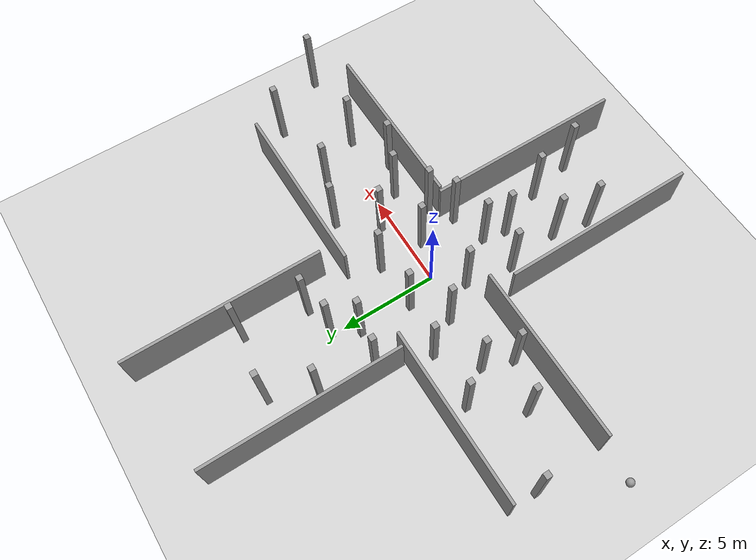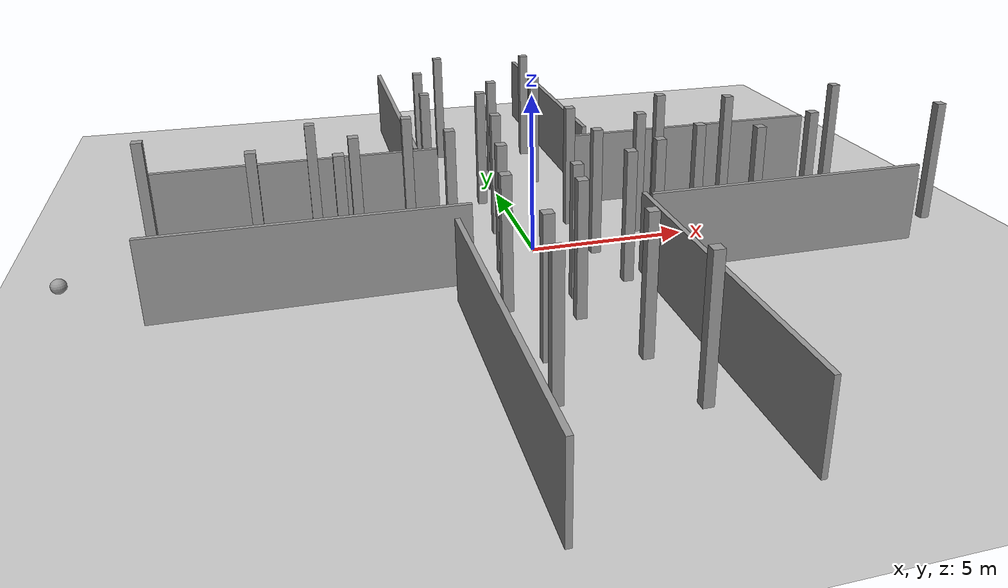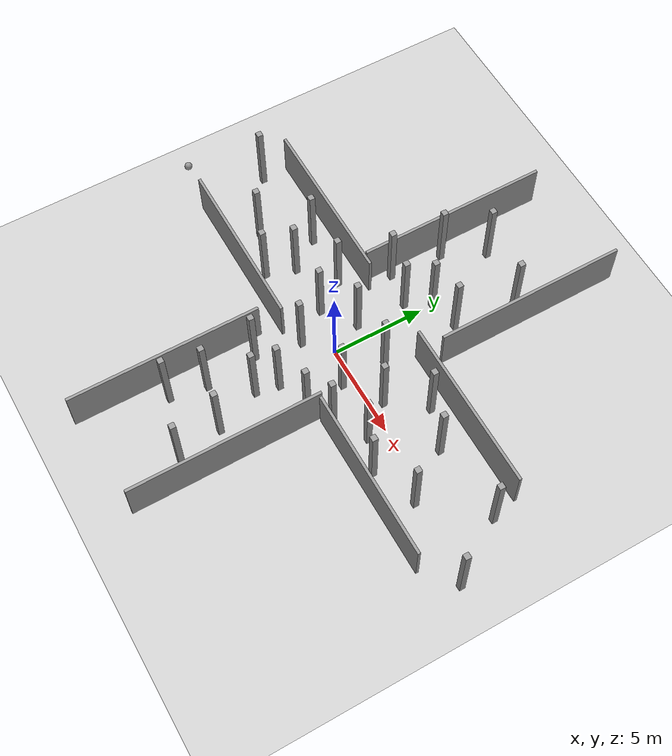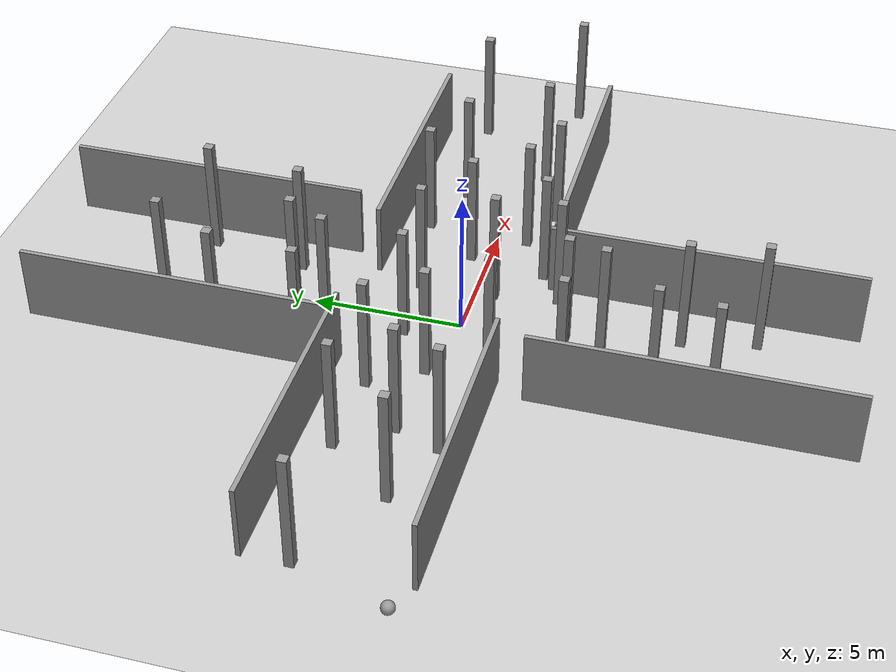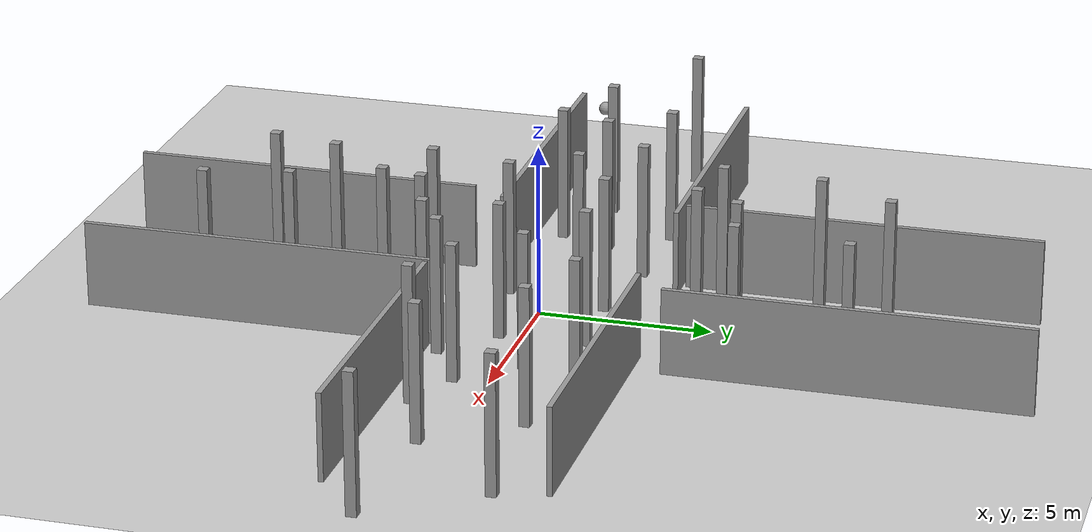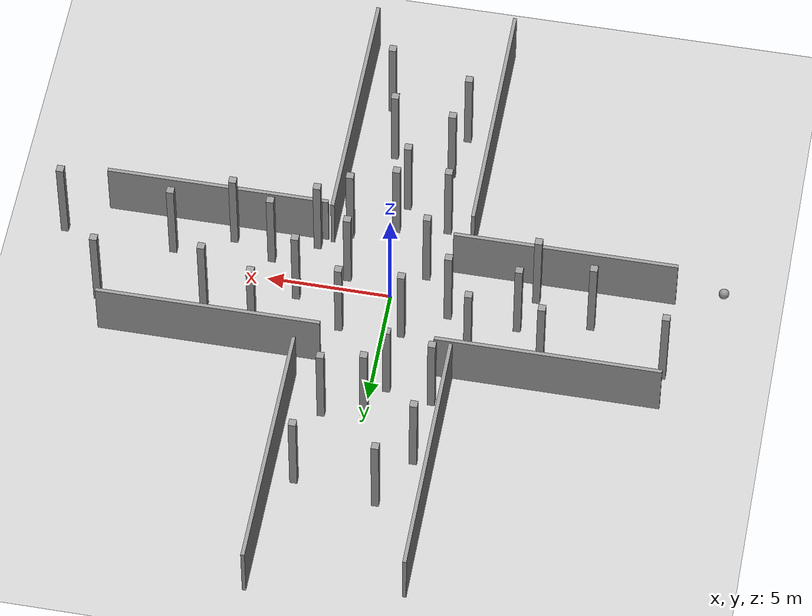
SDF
<sdf version="1.6">
 <world name="default">
  <light name="sun" type="directional">
   <pose>0 0 10 0 -0 0</pose>
   <diffuse>0.8 0.8 0.8 1</diffuse>
   <specular>0.2 0.2 0.2 1</specular>
   <attenuation>
    <range>1000</range>
    <constant>0.9</constant>
    <linear>0.01</linear>
    <quadratic>0.001</quadratic>
   </attenuation>
   <direction>-0.5 0.1 -0.9</direction>
  </light>
  <model name="ground_plane">
   <static>1</static>
   <link name="link">
    <collision name="collision">
     <geometry><plane><normal>0 0 1</normal><size>100 100</size></plane></geometry>
     <surface><friction><ode><mu>100</mu><mu2>50</mu2></ode></friction></surface>
    </collision>
    <visual name="visual">
     <cast_shadows>0</cast_shadows>
     <geometry><plane><normal>0 0 1</normal><size>100 100</size></plane></geometry>
     <material>
      <script><uri>file://media/materials/scripts/gazebo.material</uri><name>Gazebo/Grey</name></script>
     </material>
    </visual>
   </link>
  </model>
  <gravity>0 0 -9.8</gravity>
  <magnetic_field>6e-06 2.3e-05 -4.2e-05</magnetic_field>
  <atmosphere type="adiabatic"/>
  <physics name="default_physics" default="0" type="ode">
   <max_step_size>0.001</max_step_size>
   <real_time_factor>1</real_time_factor>
   <real_time_update_rate>1000</real_time_update_rate>
  </physics>
  <scene><ambient>0.4 0.4 0.4 1</ambient><background>0.7 0.7 0.7 1</background><shadows>1</shadows></scene>
  <spherical_coordinates>
   <surface_model>EARTH_WGS84</surface_model>
   <latitude_deg>0</latitude_deg>
   <longitude_deg>0</longitude_deg>
   <elevation>0</elevation>
   <heading_deg>0</heading_deg>
  </spherical_coordinates>
  <model name="Untitled">
   <pose>-6.85388 3.37469 0 0 -0 0</pose>
   <link name="Wall_1">
    <collision name="Wall_1_Collision">
     <geometry><box><size>9 0.15 2.5</size></box></geometry>
     <pose>0 0 1.25 0 -0 0</pose>
    </collision>
    <visual name="Wall_1_Visual">
     <pose>0 0 1.25 0 -0 0</pose>
     <geometry><box><size>9 0.15 2.5</size></box></geometry>
     <material>
      <script><uri>file://media/materials/scripts/gazebo.material</uri><name>Gazebo/Grey</name></script>
      <ambient>1 1 1 1</ambient>
     </material>
     <meta><layer>0</layer></meta>
    </visual>
   </link>
   <static>1</static>
  </model>
  <model name="Untitled_clone">
   <pose>-6.74636 -1.72511 0 0 -0 0</pose>
   <link name="Wall_1">
    <collision name="Wall_1_Collision">
     <geometry><box><size>9 0.15 2.5</size></box></geometry>
     <pose>0 0 1.25 0 -0 0</pose>
    </collision>
    <visual name="Wall_1_Visual">
     <pose>0 0 1.25 0 -0 0</pose>
     <geometry><box><size>9 0.15 2.5</size></box></geometry>
     <material>
      <script><uri>file://media/materials/scripts/gazebo.material</uri><name>Gazebo/Grey</name></script>
      <ambient>1 1 1 1</ambient>
     </material>
     <meta><layer>0</layer></meta>
    </visual>
   </link>
   <static>1</static>
  </model>
  <model name="Untitled_clone_clone">
   <pose>7.44153 -2.41857 0 0 -0 0</pose>
   <link name="Wall_1">
    <collision name="Wall_1_Collision">
     <geometry><box><size>9 0.15 2.5</size></box></geometry>
     <pose>0 0 1.25 0 -0 0</pose>
    </collision>
    <visual name="Wall_1_Visual">
     <pose>0 0 1.25 0 -0 0</pose>
     <geometry><box><size>9 0.15 2.5</size></box></geometry>
     <material>
      <script><uri>file://media/materials/scripts/gazebo.material</uri><name>Gazebo/Grey</name></script>
      <ambient>1 1 1 1</ambient>
     </material>
     <meta><layer>0</layer></meta>
    </visual>
   </link>
   <static>1</static>
  </model>
  <model name="Untitled_clone_clone_0">
   <pose>6.68345 3.44528 0 0 -0 0</pose>
   <link name="Wall_1">
    <collision name="Wall_1_Collision">
     <geometry><box><size>9 0.15 2.5</size></box></geometry>
     <pose>0 0 1.25 0 -0 0</pose>
    </collision>
    <visual name="Wall_1_Visual">
     <pose>0 0 1.25 0 -0 0</pose>
     <geometry><box><size>9 0.15 2.5</size></box></geometry>
     <material>
      <script><uri>file://media/materials/scripts/gazebo.material</uri><name>Gazebo/Grey</name></script>
      <ambient>1 1 1 1</ambient>
     </material>
     <meta><layer>0</layer></meta>
    </visual>
   </link>
   <static>1</static>
  </model>
  <model name="Untitled_0">
   <pose>-2.85637 -7.82972 0 0 -0 0</pose>
   <link name="Wall_3">
    <collision name="Wall_3_Collision">
     <geometry><box><size>10.25 0.15 2.5</size></box></geometry>
     <pose>0 0 1.25 0 -0 0</pose>
    </collision>
    <visual name="Wall_3_Visual">
     <pose>0 0 1.25 0 -0 0</pose>
     <geometry><box><size>10.25 0.15 2.5</size></box></geometry>
     <material>
      <script><uri>file://media/materials/scripts/gazebo.material</uri><name>Gazebo/Grey</name></script>
      <ambient>1 1 1 1</ambient>
     </material>
     <meta><layer>0</layer></meta>
    </visual>
    <pose>0 0 0 0 -0 -1.5708</pose>
   </link>
   <static>1</static>
  </model>
  <model name="Untitled_0_clone">
   <pose>2.75566 -7.3862 0 0 -0 0</pose>
   <link name="Wall_3">
    <collision name="Wall_3_Collision">
     <geometry><box><size>10.25 0.15 2.5</size></box></geometry>
     <pose>0 0 1.25 0 -0 0</pose>
    </collision>
    <visual name="Wall_3_Visual">
     <pose>0 0 1.25 0 -0 0</pose>
     <geometry><box><size>10.25 0.15 2.5</size></box></geometry>
     <material>
      <script><uri>file://media/materials/scripts/gazebo.material</uri><name>Gazebo/Grey</name></script>
      <ambient>1 1 1 1</ambient>
     </material>
     <meta><layer>0</layer></meta>
    </visual>
    <pose>0 0 0 0 -0 -1.5708</pose>
   </link>
   <static>1</static>
  </model>
  <model name="Untitled_0_clone_0">
   <pose>-3.02847 8.65549 0 0 -0 0</pose>
   <link name="Wall_3">
    <collision name="Wall_3_Collision">
     <geometry><box><size>10.25 0.15 2.5</size></box></geometry>
     <pose>0 0 1.25 0 -0 0</pose>
    </collision>
    <visual name="Wall_3_Visual">
     <pose>0 0 1.25 0 -0 0</pose>
     <geometry><box><size>10.25 0.15 2.5</size></box></geometry>
     <material>
      <script><uri>file://media/materials/scripts/gazebo.material</uri><name>Gazebo/Grey</name></script>
      <ambient>1 1 1 1</ambient>
     </material>
     <meta><layer>0</layer></meta>
    </visual>
    <pose>0 0 0 0 -0 -1.5708</pose>
   </link>
   <static>1</static>
  </model>
  <model name="Untitled_0_clone_1">
   <pose>3.06538 9.43333 0 0 -0 0</pose>
   <link name="Wall_3">
    <collision name="Wall_3_Collision">
     <geometry><box><size>10.25 0.15 2.5</size></box></geometry>
     <pose>0 0 1.25 0 -0 0</pose>
    </collision>
    <visual name="Wall_3_Visual">
     <pose>0 0 1.25 0 -0 0</pose>
     <geometry><box><size>10.25 0.15 2.5</size></box></geometry>
     <material>
      <script><uri>file://media/materials/scripts/gazebo.material</uri><name>Gazebo/Grey</name></script>
      <ambient>1 1 1 1</ambient>
     </material>
     <meta><layer>0</layer></meta>
    </visual>
    <pose>0 0 0 0 -0 -1.5708</pose>
   </link>
   <static>1</static>
  </model>
  <audio><device>default</device></audio>
  <model name="unit_box_clone_clone_24">
   <link name="link">
    <inertial>
     <mass>1000</mass>
     <inertia><ixx>1340.83</ixx><ixy>0</ixy><ixz>0</ixz><iyy>1340.83</iyy><iyz>0</iyz><izz>15</izz></inertia>
    </inertial>
    <visual name="visual">
     <geometry><box><size>0.3 0.3 4</size></box></geometry>
     <material>
      <script><name>Gazebo/Grey</name><uri>file://media/materials/scripts/gazebo.material</uri></script>
      <shader type="pixel"><normal_map>__default__</normal_map></shader>
      <ambient>0.3 0.3 0.3 1</ambient>
      <diffuse>0.7 0.7 0.7 1</diffuse>
      <specular>0.01 0.01 0.01 1</specular>
      <emissive>0 0 0 1</emissive>
     </material>
    </visual>
    <collision name="collision">
     <geometry><box><size>0.3 0.3 4</size></box></geometry>
     <surface>
      <friction>
       <ode><mu>1</mu><mu2>1</mu2><fdir1>0 0 0</fdir1><slip1>0</slip1><slip2>0</slip2></ode>
       <torsional>
        <coefficient>1</coefficient>
        <patch_radius>0</patch_radius>
        <surface_radius>0</surface_radius>
        <use_patch_radius>1</use_patch_radius>
        <ode><slip>0</slip></ode>
       </torsional>
      </friction>
      <bounce><restitution_coefficient>0</restitution_coefficient><threshold>1e+06</threshold></bounce>
      <contact>
       <collide_without_contact>0</collide_without_contact>
       <collide_without_contact_bitmask>1</collide_without_contact_bitmask>
       <collide_bitmask>1</collide_bitmask>
       <ode>
        <soft_cfm>0</soft_cfm>
        <soft_erp>0.2</soft_erp>
        <kp>1e+13</kp>
        <kd>1</kd>
        <max_vel>0.01</max_vel>
        <min_depth>0</min_depth>
       </ode>
       <bullet>
        <split_impulse>1</split_impulse>
        <split_impulse_penetration_threshold>-0.01</split_impulse_penetration_threshold>
        <soft_cfm>0</soft_cfm>
        <soft_erp>0.2</soft_erp>
        <kp>1e+13</kp>
        <kd>1</kd>
       </bullet>
      </contact>
     </surface>
    </collision>
   </link>
   <static>0</static>
   <pose>-11.2321 1.86882 2 7e-06 -1e-06 -0.002931</pose>
  </model>
  <model name="unit_box_clone_clone_24_clone">
   <link name="link">
    <inertial>
     <mass>1000</mass>
     <inertia><ixx>1340.83</ixx><ixy>0</ixy><ixz>0</ixz><iyy>1340.83</iyy><iyz>0</iyz><izz>15</izz></inertia>
    </inertial>
    <visual name="visual">
     <geometry><box><size>0.3 0.3 4</size></box></geometry>
     <material>
      <script><name>Gazebo/Grey</name><uri>file://media/materials/scripts/gazebo.material</uri></script>
      <shader type="pixel"><normal_map>__default__</normal_map></shader>
      <ambient>0.3 0.3 0.3 1</ambient>
      <diffuse>0.7 0.7 0.7 1</diffuse>
      <specular>0.01 0.01 0.01 1</specular>
      <emissive>0 0 0 1</emissive>
     </material>
    </visual>
    <collision name="collision">
     <geometry><box><size>0.3 0.3 4</size></box></geometry>
     <surface>
      <friction>
       <ode><mu>1</mu><mu2>1</mu2><fdir1>0 0 0</fdir1><slip1>0</slip1><slip2>0</slip2></ode>
       <torsional>
        <coefficient>1</coefficient>
        <patch_radius>0</patch_radius>
        <surface_radius>0</surface_radius>
        <use_patch_radius>1</use_patch_radius>
        <ode><slip>0</slip></ode>
       </torsional>
      </friction>
      <bounce><restitution_coefficient>0</restitution_coefficient><threshold>1e+06</threshold></bounce>
      <contact>
       <collide_without_contact>0</collide_without_contact>
       <collide_without_contact_bitmask>1</collide_without_contact_bitmask>
       <collide_bitmask>1</collide_bitmask>
       <ode>
        <soft_cfm>0</soft_cfm>
        <soft_erp>0.2</soft_erp>
        <kp>1e+13</kp>
        <kd>1</kd>
        <max_vel>0.01</max_vel>
        <min_depth>0</min_depth>
       </ode>
       <bullet>
        <split_impulse>1</split_impulse>
        <split_impulse_penetration_threshold>-0.01</split_impulse_penetration_threshold>
        <soft_cfm>0</soft_cfm>
        <soft_erp>0.2</soft_erp>
        <kp>1e+13</kp>
        <kd>1</kd>
       </bullet>
      </contact>
     </surface>
    </collision>
   </link>
   <static>0</static>
   <pose>-2.42599 0.511197 2 1.4e-05 -0 -0.002924</pose>
  </model>
  <model name="unit_box_clone_clone_24_clone_0">
   <link name="link">
    <inertial>
     <mass>1000</mass>
     <inertia><ixx>1340.83</ixx><ixy>0</ixy><ixz>0</ixz><iyy>1340.83</iyy><iyz>0</iyz><izz>15</izz></inertia>
    </inertial>
    <visual name="visual">
     <geometry><box><size>0.3 0.3 4</size></box></geometry>
     <material>
      <script><name>Gazebo/Grey</name><uri>file://media/materials/scripts/gazebo.material</uri></script>
      <shader type="pixel"><normal_map>__default__</normal_map></shader>
      <ambient>0.3 0.3 0.3 1</ambient>
      <diffuse>0.7 0.7 0.7 1</diffuse>
      <specular>0.01 0.01 0.01 1</specular>
      <emissive>0 0 0 1</emissive>
     </material>
    </visual>
    <collision name="collision">
     <geometry><box><size>0.3 0.3 4</size></box></geometry>
     <surface>
      <friction>
       <ode><mu>1</mu><mu2>1</mu2><fdir1>0 0 0</fdir1><slip1>0</slip1><slip2>0</slip2></ode>
       <torsional>
        <coefficient>1</coefficient>
        <patch_radius>0</patch_radius>
        <surface_radius>0</surface_radius>
        <use_patch_radius>1</use_patch_radius>
        <ode><slip>0</slip></ode>
       </torsional>
      </friction>
      <bounce><restitution_coefficient>0</restitution_coefficient><threshold>1e+06</threshold></bounce>
      <contact>
       <collide_without_contact>0</collide_without_contact>
       <collide_without_contact_bitmask>1</collide_without_contact_bitmask>
       <collide_bitmask>1</collide_bitmask>
       <ode>
        <soft_cfm>0</soft_cfm>
        <soft_erp>0.2</soft_erp>
        <kp>1e+13</kp>
        <kd>1</kd>
        <max_vel>0.01</max_vel>
        <min_depth>0</min_depth>
       </ode>
       <bullet>
        <split_impulse>1</split_impulse>
        <split_impulse_penetration_threshold>-0.01</split_impulse_penetration_threshold>
        <soft_cfm>0</soft_cfm>
        <soft_erp>0.2</soft_erp>
        <kp>1e+13</kp>
        <kd>1</kd>
       </bullet>
      </contact>
     </surface>
    </collision>
   </link>
   <static>0</static>
   <pose>-1.26208 -1.22117 2 6e-06 -0 -0.002932</pose>
  </model>
  <model name="unit_box_clone_clone_24_clone_1">
   <link name="link">
    <inertial>
     <mass>1000</mass>
     <inertia><ixx>1340.83</ixx><ixy>0</ixy><ixz>0</ixz><iyy>1340.83</iyy><iyz>0</iyz><izz>15</izz></inertia>
    </inertial>
    <visual name="visual">
     <geometry><box><size>0.3 0.3 4</size></box></geometry>
     <material>
      <script><name>Gazebo/Grey</name><uri>file://media/materials/scripts/gazebo.material</uri></script>
      <shader type="pixel"><normal_map>__default__</normal_map></shader>
      <ambient>0.3 0.3 0.3 1</ambient>
      <diffuse>0.7 0.7 0.7 1</diffuse>
      <specular>0.01 0.01 0.01 1</specular>
      <emissive>0 0 0 1</emissive>
     </material>
    </visual>
    <collision name="collision">
     <geometry><box><size>0.3 0.3 4</size></box></geometry>
     <surface>
      <friction>
       <ode><mu>1</mu><mu2>1</mu2><fdir1>0 0 0</fdir1><slip1>0</slip1><slip2>0</slip2></ode>
       <torsional>
        <coefficient>1</coefficient>
        <patch_radius>0</patch_radius>
        <surface_radius>0</surface_radius>
        <use_patch_radius>1</use_patch_radius>
        <ode><slip>0</slip></ode>
       </torsional>
      </friction>
      <bounce><restitution_coefficient>0</restitution_coefficient><threshold>1e+06</threshold></bounce>
      <contact>
       <collide_without_contact>0</collide_without_contact>
       <collide_without_contact_bitmask>1</collide_without_contact_bitmask>
       <collide_bitmask>1</collide_bitmask>
       <ode>
        <soft_cfm>0</soft_cfm>
        <soft_erp>0.2</soft_erp>
        <kp>1e+13</kp>
        <kd>1</kd>
        <max_vel>0.01</max_vel>
        <min_depth>0</min_depth>
       </ode>
       <bullet>
        <split_impulse>1</split_impulse>
        <split_impulse_penetration_threshold>-0.01</split_impulse_penetration_threshold>
        <soft_cfm>0</soft_cfm>
        <soft_erp>0.2</soft_erp>
        <kp>1e+13</kp>
        <kd>1</kd>
       </bullet>
      </contact>
     </surface>
    </collision>
   </link>
   <static>0</static>
   <pose>1.73831 1.8342 2 -2e-06 6e-06 -0.002921</pose>
  </model>
  <model name="unit_box_clone_clone_24_clone_2">
   <link name="link">
    <inertial>
     <mass>1000</mass>
     <inertia><ixx>1340.83</ixx><ixy>0</ixy><ixz>0</ixz><iyy>1340.83</iyy><iyz>0</iyz><izz>15</izz></inertia>
    </inertial>
    <visual name="visual">
     <geometry><box><size>0.3 0.3 4</size></box></geometry>
     <material>
      <script><name>Gazebo/Grey</name><uri>file://media/materials/scripts/gazebo.material</uri></script>
      <shader type="pixel"><normal_map>__default__</normal_map></shader>
      <ambient>0.3 0.3 0.3 1</ambient>
      <diffuse>0.7 0.7 0.7 1</diffuse>
      <specular>0.01 0.01 0.01 1</specular>
      <emissive>0 0 0 1</emissive>
     </material>
    </visual>
    <collision name="collision">
     <geometry><box><size>0.3 0.3 4</size></box></geometry>
     <surface>
      <friction>
       <ode><mu>1</mu><mu2>1</mu2><fdir1>0 0 0</fdir1><slip1>0</slip1><slip2>0</slip2></ode>
       <torsional>
        <coefficient>1</coefficient>
        <patch_radius>0</patch_radius>
        <surface_radius>0</surface_radius>
        <use_patch_radius>1</use_patch_radius>
        <ode><slip>0</slip></ode>
       </torsional>
      </friction>
      <bounce><restitution_coefficient>0</restitution_coefficient><threshold>1e+06</threshold></bounce>
      <contact>
       <collide_without_contact>0</collide_without_contact>
       <collide_without_contact_bitmask>1</collide_without_contact_bitmask>
       <collide_bitmask>1</collide_bitmask>
       <ode>
        <soft_cfm>0</soft_cfm>
        <soft_erp>0.2</soft_erp>
        <kp>1e+13</kp>
        <kd>1</kd>
        <max_vel>0.01</max_vel>
        <min_depth>0</min_depth>
       </ode>
       <bullet>
        <split_impulse>1</split_impulse>
        <split_impulse_penetration_threshold>-0.01</split_impulse_penetration_threshold>
        <soft_cfm>0</soft_cfm>
        <soft_erp>0.2</soft_erp>
        <kp>1e+13</kp>
        <kd>1</kd>
       </bullet>
      </contact>
     </surface>
    </collision>
   </link>
   <static>0</static>
   <pose>-0.653803 4.40188 2 -0 -0 -0.002928</pose>
  </model>
  <model name="unit_box_clone_clone_24_clone_3">
   <link name="link">
    <inertial>
     <mass>1000</mass>
     <inertia><ixx>1340.83</ixx><ixy>0</ixy><ixz>0</ixz><iyy>1340.83</iyy><iyz>0</iyz><izz>15</izz></inertia>
    </inertial>
    <visual name="visual">
     <geometry><box><size>0.3 0.3 4</size></box></geometry>
     <material>
      <script><name>Gazebo/Grey</name><uri>file://media/materials/scripts/gazebo.material</uri></script>
      <shader type="pixel"><normal_map>__default__</normal_map></shader>
      <ambient>0.3 0.3 0.3 1</ambient>
      <diffuse>0.7 0.7 0.7 1</diffuse>
      <specular>0.01 0.01 0.01 1</specular>
      <emissive>0 0 0 1</emissive>
     </material>
    </visual>
    <collision name="collision">
     <geometry><box><size>0.3 0.3 4</size></box></geometry>
     <surface>
      <friction>
       <ode><mu>1</mu><mu2>1</mu2><fdir1>0 0 0</fdir1><slip1>0</slip1><slip2>0</slip2></ode>
       <torsional>
        <coefficient>1</coefficient>
        <patch_radius>0</patch_radius>
        <surface_radius>0</surface_radius>
        <use_patch_radius>1</use_patch_radius>
        <ode><slip>0</slip></ode>
       </torsional>
      </friction>
      <bounce><restitution_coefficient>0</restitution_coefficient><threshold>1e+06</threshold></bounce>
      <contact>
       <collide_without_contact>0</collide_without_contact>
       <collide_without_contact_bitmask>1</collide_without_contact_bitmask>
       <collide_bitmask>1</collide_bitmask>
       <ode>
        <soft_cfm>0</soft_cfm>
        <soft_erp>0.2</soft_erp>
        <kp>1e+13</kp>
        <kd>1</kd>
        <max_vel>0.01</max_vel>
        <min_depth>0</min_depth>
       </ode>
       <bullet>
        <split_impulse>1</split_impulse>
        <split_impulse_penetration_threshold>-0.01</split_impulse_penetration_threshold>
        <soft_cfm>0</soft_cfm>
        <soft_erp>0.2</soft_erp>
        <kp>1e+13</kp>
        <kd>1</kd>
       </bullet>
      </contact>
     </surface>
    </collision>
   </link>
   <static>0</static>
   <pose>1.67139 5.986 2 4e-06 -1e-06 -0.002935</pose>
  </model>
  <model name="unit_box_clone_clone_24_clone_4">
   <link name="link">
    <inertial>
     <mass>1000</mass>
     <inertia><ixx>1340.83</ixx><ixy>0</ixy><ixz>0</ixz><iyy>1340.83</iyy><iyz>0</iyz><izz>15</izz></inertia>
    </inertial>
    <visual name="visual">
     <geometry><box><size>0.3 0.3 4</size></box></geometry>
     <material>
      <script><name>Gazebo/Grey</name><uri>file://media/materials/scripts/gazebo.material</uri></script>
      <shader type="pixel"><normal_map>__default__</normal_map></shader>
      <ambient>0.3 0.3 0.3 1</ambient>
      <diffuse>0.7 0.7 0.7 1</diffuse>
      <specular>0.01 0.01 0.01 1</specular>
      <emissive>0 0 0 1</emissive>
     </material>
    </visual>
    <collision name="collision">
     <geometry><box><size>0.3 0.3 4</size></box></geometry>
     <surface>
      <friction>
       <ode><mu>1</mu><mu2>1</mu2><fdir1>0 0 0</fdir1><slip1>0</slip1><slip2>0</slip2></ode>
       <torsional>
        <coefficient>1</coefficient>
        <patch_radius>0</patch_radius>
        <surface_radius>0</surface_radius>
        <use_patch_radius>1</use_patch_radius>
        <ode><slip>0</slip></ode>
       </torsional>
      </friction>
      <bounce><restitution_coefficient>0</restitution_coefficient><threshold>1e+06</threshold></bounce>
      <contact>
       <collide_without_contact>0</collide_without_contact>
       <collide_without_contact_bitmask>1</collide_without_contact_bitmask>
       <collide_bitmask>1</collide_bitmask>
       <ode>
        <soft_cfm>0</soft_cfm>
        <soft_erp>0.2</soft_erp>
        <kp>1e+13</kp>
        <kd>1</kd>
        <max_vel>0.01</max_vel>
        <min_depth>0</min_depth>
       </ode>
       <bullet>
        <split_impulse>1</split_impulse>
        <split_impulse_penetration_threshold>-0.01</split_impulse_penetration_threshold>
        <soft_cfm>0</soft_cfm>
        <soft_erp>0.2</soft_erp>
        <kp>1e+13</kp>
        <kd>1</kd>
       </bullet>
      </contact>
     </surface>
    </collision>
   </link>
   <static>0</static>
   <pose>-2.28629 7.58681 2 -1.8e-05 -0 -0.002925</pose>
  </model>
  <model name="unit_box_clone_clone_24_clone_5">
   <link name="link">
    <inertial>
     <mass>1000</mass>
     <inertia><ixx>1340.83</ixx><ixy>0</ixy><ixz>0</ixz><iyy>1340.83</iyy><iyz>0</iyz><izz>15</izz></inertia>
    </inertial>
    <visual name="visual">
     <geometry><box><size>0.3 0.3 4</size></box></geometry>
     <material>
      <script><name>Gazebo/Grey</name><uri>file://media/materials/scripts/gazebo.material</uri></script>
      <shader type="pixel"><normal_map>__default__</normal_map></shader>
      <ambient>0.3 0.3 0.3 1</ambient>
      <diffuse>0.7 0.7 0.7 1</diffuse>
      <specular>0.01 0.01 0.01 1</specular>
      <emissive>0 0 0 1</emissive>
     </material>
    </visual>
    <collision name="collision">
     <geometry><box><size>0.3 0.3 4</size></box></geometry>
     <surface>
      <friction>
       <ode><mu>1</mu><mu2>1</mu2><fdir1>0 0 0</fdir1><slip1>0</slip1><slip2>0</slip2></ode>
       <torsional>
        <coefficient>1</coefficient>
        <patch_radius>0</patch_radius>
        <surface_radius>0</surface_radius>
        <use_patch_radius>1</use_patch_radius>
        <ode><slip>0</slip></ode>
       </torsional>
      </friction>
      <bounce><restitution_coefficient>0</restitution_coefficient><threshold>1e+06</threshold></bounce>
      <contact>
       <collide_without_contact>0</collide_without_contact>
       <collide_without_contact_bitmask>1</collide_without_contact_bitmask>
       <collide_bitmask>1</collide_bitmask>
       <ode>
        <soft_cfm>0</soft_cfm>
        <soft_erp>0.2</soft_erp>
        <kp>1e+13</kp>
        <kd>1</kd>
        <max_vel>0.01</max_vel>
        <min_depth>0</min_depth>
       </ode>
       <bullet>
        <split_impulse>1</split_impulse>
        <split_impulse_penetration_threshold>-0.01</split_impulse_penetration_threshold>
        <soft_cfm>0</soft_cfm>
        <soft_erp>0.2</soft_erp>
        <kp>1e+13</kp>
        <kd>1</kd>
       </bullet>
      </contact>
     </surface>
    </collision>
   </link>
   <static>0</static>
   <pose>2.13376 9.26118 2 0 -1e-05 -0.002932</pose>
  </model>
  <model name="unit_box_clone_clone_24_clone_6">
   <link name="link">
    <inertial>
     <mass>1000</mass>
     <inertia><ixx>1340.83</ixx><ixy>0</ixy><ixz>0</ixz><iyy>1340.83</iyy><iyz>0</iyz><izz>15</izz></inertia>
    </inertial>
    <visual name="visual">
     <geometry><box><size>0.3 0.3 4</size></box></geometry>
     <material>
      <script><name>Gazebo/Grey</name><uri>file://media/materials/scripts/gazebo.material</uri></script>
      <shader type="pixel"><normal_map>__default__</normal_map></shader>
      <ambient>0.3 0.3 0.3 1</ambient>
      <diffuse>0.7 0.7 0.7 1</diffuse>
      <specular>0.01 0.01 0.01 1</specular>
      <emissive>0 0 0 1</emissive>
     </material>
    </visual>
    <collision name="collision">
     <geometry><box><size>0.3 0.3 4</size></box></geometry>
     <surface>
      <friction>
       <ode><mu>1</mu><mu2>1</mu2><fdir1>0 0 0</fdir1><slip1>0</slip1><slip2>0</slip2></ode>
       <torsional>
        <coefficient>1</coefficient>
        <patch_radius>0</patch_radius>
        <surface_radius>0</surface_radius>
        <use_patch_radius>1</use_patch_radius>
        <ode><slip>0</slip></ode>
       </torsional>
      </friction>
      <bounce><restitution_coefficient>0</restitution_coefficient><threshold>1e+06</threshold></bounce>
      <contact>
       <collide_without_contact>0</collide_without_contact>
       <collide_without_contact_bitmask>1</collide_without_contact_bitmask>
       <collide_bitmask>1</collide_bitmask>
       <ode>
        <soft_cfm>0</soft_cfm>
        <soft_erp>0.2</soft_erp>
        <kp>1e+13</kp>
        <kd>1</kd>
        <max_vel>0.01</max_vel>
        <min_depth>0</min_depth>
       </ode>
       <bullet>
        <split_impulse>1</split_impulse>
        <split_impulse_penetration_threshold>-0.01</split_impulse_penetration_threshold>
        <soft_cfm>0</soft_cfm>
        <soft_erp>0.2</soft_erp>
        <kp>1e+13</kp>
        <kd>1</kd>
       </bullet>
      </contact>
     </surface>
    </collision>
   </link>
   <static>0</static>
   <pose>-1.17803 9.7513 2 0 0 -0.002937</pose>
  </model>
  <model name="unit_box_clone_clone_24_clone_7">
   <link name="link">
    <inertial>
     <mass>1000</mass>
     <inertia><ixx>1340.83</ixx><ixy>0</ixy><ixz>0</ixz><iyy>1340.83</iyy><iyz>0</iyz><izz>15</izz></inertia>
    </inertial>
    <visual name="visual">
     <geometry><box><size>0.3 0.3 4</size></box></geometry>
     <material>
      <script><name>Gazebo/Grey</name><uri>file://media/materials/scripts/gazebo.material</uri></script>
      <shader type="pixel"><normal_map>__default__</normal_map></shader>
      <ambient>0.3 0.3 0.3 1</ambient>
      <diffuse>0.7 0.7 0.7 1</diffuse>
      <specular>0.01 0.01 0.01 1</specular>
      <emissive>0 0 0 1</emissive>
     </material>
    </visual>
    <collision name="collision">
     <geometry><box><size>0.3 0.3 4</size></box></geometry>
     <surface>
      <friction>
       <ode><mu>1</mu><mu2>1</mu2><fdir1>0 0 0</fdir1><slip1>0</slip1><slip2>0</slip2></ode>
       <torsional>
        <coefficient>1</coefficient>
        <patch_radius>0</patch_radius>
        <surface_radius>0</surface_radius>
        <use_patch_radius>1</use_patch_radius>
        <ode><slip>0</slip></ode>
       </torsional>
      </friction>
      <bounce><restitution_coefficient>0</restitution_coefficient><threshold>1e+06</threshold></bounce>
      <contact>
       <collide_without_contact>0</collide_without_contact>
       <collide_without_contact_bitmask>1</collide_without_contact_bitmask>
       <collide_bitmask>1</collide_bitmask>
       <ode>
        <soft_cfm>0</soft_cfm>
        <soft_erp>0.2</soft_erp>
        <kp>1e+13</kp>
        <kd>1</kd>
        <max_vel>0.01</max_vel>
        <min_depth>0</min_depth>
       </ode>
       <bullet>
        <split_impulse>1</split_impulse>
        <split_impulse_penetration_threshold>-0.01</split_impulse_penetration_threshold>
        <soft_cfm>0</soft_cfm>
        <soft_erp>0.2</soft_erp>
        <kp>1e+13</kp>
        <kd>1</kd>
       </bullet>
      </contact>
     </surface>
    </collision>
   </link>
   <static>0</static>
   <pose>-8.10757 0.03817 2.00001 0 4e-05 -0.002926</pose>
  </model>
  <model name="unit_box_clone_clone_24_clone_8">
   <link name="link">
    <inertial>
     <mass>1000</mass>
     <inertia><ixx>1340.83</ixx><ixy>0</ixy><ixz>0</ixz><iyy>1340.83</iyy><iyz>0</iyz><izz>15</izz></inertia>
    </inertial>
    <visual name="visual">
     <geometry><box><size>0.3 0.3 4</size></box></geometry>
     <material>
      <script><name>Gazebo/Grey</name><uri>file://media/materials/scripts/gazebo.material</uri></script>
      <shader type="pixel"><normal_map>__default__</normal_map></shader>
      <ambient>0.3 0.3 0.3 1</ambient>
      <diffuse>0.7 0.7 0.7 1</diffuse>
      <specular>0.01 0.01 0.01 1</specular>
      <emissive>0 0 0 1</emissive>
     </material>
    </visual>
    <collision name="collision">
     <geometry><box><size>0.3 0.3 4</size></box></geometry>
     <surface>
      <friction>
       <ode><mu>1</mu><mu2>1</mu2><fdir1>0 0 0</fdir1><slip1>0</slip1><slip2>0</slip2></ode>
       <torsional>
        <coefficient>1</coefficient>
        <patch_radius>0</patch_radius>
        <surface_radius>0</surface_radius>
        <use_patch_radius>1</use_patch_radius>
        <ode><slip>0</slip></ode>
       </torsional>
      </friction>
      <bounce><restitution_coefficient>0</restitution_coefficient><threshold>1e+06</threshold></bounce>
      <contact>
       <collide_without_contact>0</collide_without_contact>
       <collide_without_contact_bitmask>1</collide_without_contact_bitmask>
       <collide_bitmask>1</collide_bitmask>
       <ode>
        <soft_cfm>0</soft_cfm>
        <soft_erp>0.2</soft_erp>
        <kp>1e+13</kp>
        <kd>1</kd>
        <max_vel>0.01</max_vel>
        <min_depth>0</min_depth>
       </ode>
       <bullet>
        <split_impulse>1</split_impulse>
        <split_impulse_penetration_threshold>-0.01</split_impulse_penetration_threshold>
        <soft_cfm>0</soft_cfm>
        <soft_erp>0.2</soft_erp>
        <kp>1e+13</kp>
        <kd>1</kd>
       </bullet>
      </contact>
     </surface>
    </collision>
   </link>
   <static>0</static>
   <pose>-6.39947 2.26061 2 0 4e-06 -0.002923</pose>
  </model>
  <model name="unit_box_clone_clone_24_clone_9">
   <link name="link">
    <inertial>
     <mass>1000</mass>
     <inertia><ixx>1340.83</ixx><ixy>0</ixy><ixz>0</ixz><iyy>1340.83</iyy><iyz>0</iyz><izz>15</izz></inertia>
    </inertial>
    <visual name="visual">
     <geometry><box><size>0.3 0.3 4</size></box></geometry>
     <material>
      <script><name>Gazebo/Grey</name><uri>file://media/materials/scripts/gazebo.material</uri></script>
      <shader type="pixel"><normal_map>__default__</normal_map></shader>
      <ambient>0.3 0.3 0.3 1</ambient>
      <diffuse>0.7 0.7 0.7 1</diffuse>
      <specular>0.01 0.01 0.01 1</specular>
      <emissive>0 0 0 1</emissive>
     </material>
    </visual>
    <collision name="collision">
     <geometry><box><size>0.3 0.3 4</size></box></geometry>
     <surface>
      <friction>
       <ode><mu>1</mu><mu2>1</mu2><fdir1>0 0 0</fdir1><slip1>0</slip1><slip2>0</slip2></ode>
       <torsional>
        <coefficient>1</coefficient>
        <patch_radius>0</patch_radius>
        <surface_radius>0</surface_radius>
        <use_patch_radius>1</use_patch_radius>
        <ode><slip>0</slip></ode>
       </torsional>
      </friction>
      <bounce><restitution_coefficient>0</restitution_coefficient><threshold>1e+06</threshold></bounce>
      <contact>
       <collide_without_contact>0</collide_without_contact>
       <collide_without_contact_bitmask>1</collide_without_contact_bitmask>
       <collide_bitmask>1</collide_bitmask>
       <ode>
        <soft_cfm>0</soft_cfm>
        <soft_erp>0.2</soft_erp>
        <kp>1e+13</kp>
        <kd>1</kd>
        <max_vel>0.01</max_vel>
        <min_depth>0</min_depth>
       </ode>
       <bullet>
        <split_impulse>1</split_impulse>
        <split_impulse_penetration_threshold>-0.01</split_impulse_penetration_threshold>
        <soft_cfm>0</soft_cfm>
        <soft_erp>0.2</soft_erp>
        <kp>1e+13</kp>
        <kd>1</kd>
       </bullet>
      </contact>
     </surface>
    </collision>
   </link>
   <static>0</static>
   <pose>-5.77278 -0.868819 2 2e-06 -0 -0.002932</pose>
  </model>
  <model name="unit_box_clone_clone_24_clone_10">
   <link name="link">
    <inertial>
     <mass>1000</mass>
     <inertia><ixx>1340.83</ixx><ixy>0</ixy><ixz>0</ixz><iyy>1340.83</iyy><iyz>0</iyz><izz>15</izz></inertia>
    </inertial>
    <visual name="visual">
     <geometry><box><size>0.3 0.3 4</size></box></geometry>
     <material>
      <script><name>Gazebo/Grey</name><uri>file://media/materials/scripts/gazebo.material</uri></script>
      <shader type="pixel"><normal_map>__default__</normal_map></shader>
      <ambient>0.3 0.3 0.3 1</ambient>
      <diffuse>0.7 0.7 0.7 1</diffuse>
      <specular>0.01 0.01 0.01 1</specular>
      <emissive>0 0 0 1</emissive>
     </material>
    </visual>
    <collision name="collision">
     <geometry><box><size>0.3 0.3 4</size></box></geometry>
     <surface>
      <friction>
       <ode><mu>1</mu><mu2>1</mu2><fdir1>0 0 0</fdir1><slip1>0</slip1><slip2>0</slip2></ode>
       <torsional>
        <coefficient>1</coefficient>
        <patch_radius>0</patch_radius>
        <surface_radius>0</surface_radius>
        <use_patch_radius>1</use_patch_radius>
        <ode><slip>0</slip></ode>
       </torsional>
      </friction>
      <bounce><restitution_coefficient>0</restitution_coefficient><threshold>1e+06</threshold></bounce>
      <contact>
       <collide_without_contact>0</collide_without_contact>
       <collide_without_contact_bitmask>1</collide_without_contact_bitmask>
       <collide_bitmask>1</collide_bitmask>
       <ode>
        <soft_cfm>0</soft_cfm>
        <soft_erp>0.2</soft_erp>
        <kp>1e+13</kp>
        <kd>1</kd>
        <max_vel>0.01</max_vel>
        <min_depth>0</min_depth>
       </ode>
       <bullet>
        <split_impulse>1</split_impulse>
        <split_impulse_penetration_threshold>-0.01</split_impulse_penetration_threshold>
        <soft_cfm>0</soft_cfm>
        <soft_erp>0.2</soft_erp>
        <kp>1e+13</kp>
        <kd>1</kd>
       </bullet>
      </contact>
     </surface>
    </collision>
   </link>
   <static>0</static>
   <pose>0.089496 -4.54654 2 -1.9e-05 -1e-06 -0.002929</pose>
  </model>
  <model name="unit_box_clone_clone_24_clone_11">
   <link name="link">
    <inertial>
     <mass>1000</mass>
     <inertia><ixx>1340.83</ixx><ixy>0</ixy><ixz>0</ixz><iyy>1340.83</iyy><iyz>0</iyz><izz>15</izz></inertia>
    </inertial>
    <visual name="visual">
     <geometry><box><size>0.3 0.3 4</size></box></geometry>
     <material>
      <script><name>Gazebo/Grey</name><uri>file://media/materials/scripts/gazebo.material</uri></script>
      <shader type="pixel"><normal_map>__default__</normal_map></shader>
      <ambient>0.3 0.3 0.3 1</ambient>
      <diffuse>0.7 0.7 0.7 1</diffuse>
      <specular>0.01 0.01 0.01 1</specular>
      <emissive>0 0 0 1</emissive>
     </material>
    </visual>
    <collision name="collision">
     <geometry><box><size>0.3 0.3 4</size></box></geometry>
     <surface>
      <friction>
       <ode><mu>1</mu><mu2>1</mu2><fdir1>0 0 0</fdir1><slip1>0</slip1><slip2>0</slip2></ode>
       <torsional>
        <coefficient>1</coefficient>
        <patch_radius>0</patch_radius>
        <surface_radius>0</surface_radius>
        <use_patch_radius>1</use_patch_radius>
        <ode><slip>0</slip></ode>
       </torsional>
      </friction>
      <bounce><restitution_coefficient>0</restitution_coefficient><threshold>1e+06</threshold></bounce>
      <contact>
       <collide_without_contact>0</collide_without_contact>
       <collide_without_contact_bitmask>1</collide_without_contact_bitmask>
       <collide_bitmask>1</collide_bitmask>
       <ode>
        <soft_cfm>0</soft_cfm>
        <soft_erp>0.2</soft_erp>
        <kp>1e+13</kp>
        <kd>1</kd>
        <max_vel>0.01</max_vel>
        <min_depth>0</min_depth>
       </ode>
       <bullet>
        <split_impulse>1</split_impulse>
        <split_impulse_penetration_threshold>-0.01</split_impulse_penetration_threshold>
        <soft_cfm>0</soft_cfm>
        <soft_erp>0.2</soft_erp>
        <kp>1e+13</kp>
        <kd>1</kd>
       </bullet>
      </contact>
     </surface>
    </collision>
   </link>
   <static>0</static>
   <pose>-1.71696 -3.61973 2 0 -1.1e-05 -0.002923</pose>
  </model>
  <model name="unit_box_clone_clone_24_clone_12">
   <link name="link">
    <inertial>
     <mass>1000</mass>
     <inertia><ixx>1340.83</ixx><ixy>0</ixy><ixz>0</ixz><iyy>1340.83</iyy><iyz>0</iyz><izz>15</izz></inertia>
    </inertial>
    <visual name="visual">
     <geometry><box><size>0.3 0.3 4</size></box></geometry>
     <material>
      <script><name>Gazebo/Grey</name><uri>file://media/materials/scripts/gazebo.material</uri></script>
      <shader type="pixel"><normal_map>__default__</normal_map></shader>
      <ambient>0.3 0.3 0.3 1</ambient>
      <diffuse>0.7 0.7 0.7 1</diffuse>
      <specular>0.01 0.01 0.01 1</specular>
      <emissive>0 0 0 1</emissive>
     </material>
    </visual>
    <collision name="collision">
     <geometry><box><size>0.3 0.3 4</size></box></geometry>
     <surface>
      <friction>
       <ode><mu>1</mu><mu2>1</mu2><fdir1>0 0 0</fdir1><slip1>0</slip1><slip2>0</slip2></ode>
       <torsional>
        <coefficient>1</coefficient>
        <patch_radius>0</patch_radius>
        <surface_radius>0</surface_radius>
        <use_patch_radius>1</use_patch_radius>
        <ode><slip>0</slip></ode>
       </torsional>
      </friction>
      <bounce><restitution_coefficient>0</restitution_coefficient><threshold>1e+06</threshold></bounce>
      <contact>
       <collide_without_contact>0</collide_without_contact>
       <collide_without_contact_bitmask>1</collide_without_contact_bitmask>
       <collide_bitmask>1</collide_bitmask>
       <ode>
        <soft_cfm>0</soft_cfm>
        <soft_erp>0.2</soft_erp>
        <kp>1e+13</kp>
        <kd>1</kd>
        <max_vel>0.01</max_vel>
        <min_depth>0</min_depth>
       </ode>
       <bullet>
        <split_impulse>1</split_impulse>
        <split_impulse_penetration_threshold>-0.01</split_impulse_penetration_threshold>
        <soft_cfm>0</soft_cfm>
        <soft_erp>0.2</soft_erp>
        <kp>1e+13</kp>
        <kd>1</kd>
       </bullet>
      </contact>
     </surface>
    </collision>
   </link>
   <static>0</static>
   <pose>1.83326 -0.615108 2 -3.4e-05 -0 -0.002931</pose>
  </model>
  <model name="unit_box_clone_clone_24_clone_13">
   <link name="link">
    <inertial>
     <mass>1000</mass>
     <inertia><ixx>1340.83</ixx><ixy>0</ixy><ixz>0</ixz><iyy>1340.83</iyy><iyz>0</iyz><izz>15</izz></inertia>
    </inertial>
    <visual name="visual">
     <geometry><box><size>0.3 0.3 4</size></box></geometry>
     <material>
      <script><name>Gazebo/Grey</name><uri>file://media/materials/scripts/gazebo.material</uri></script>
      <shader type="pixel"><normal_map>__default__</normal_map></shader>
      <ambient>0.3 0.3 0.3 1</ambient>
      <diffuse>0.7 0.7 0.7 1</diffuse>
      <specular>0.01 0.01 0.01 1</specular>
      <emissive>0 0 0 1</emissive>
     </material>
    </visual>
    <collision name="collision">
     <geometry><box><size>0.3 0.3 4</size></box></geometry>
     <surface>
      <friction>
       <ode><mu>1</mu><mu2>1</mu2><fdir1>0 0 0</fdir1><slip1>0</slip1><slip2>0</slip2></ode>
       <torsional>
        <coefficient>1</coefficient>
        <patch_radius>0</patch_radius>
        <surface_radius>0</surface_radius>
        <use_patch_radius>1</use_patch_radius>
        <ode><slip>0</slip></ode>
       </torsional>
      </friction>
      <bounce><restitution_coefficient>0</restitution_coefficient><threshold>1e+06</threshold></bounce>
      <contact>
       <collide_without_contact>0</collide_without_contact>
       <collide_without_contact_bitmask>1</collide_without_contact_bitmask>
       <collide_bitmask>1</collide_bitmask>
       <ode>
        <soft_cfm>0</soft_cfm>
        <soft_erp>0.2</soft_erp>
        <kp>1e+13</kp>
        <kd>1</kd>
        <max_vel>0.01</max_vel>
        <min_depth>0</min_depth>
       </ode>
       <bullet>
        <split_impulse>1</split_impulse>
        <split_impulse_penetration_threshold>-0.01</split_impulse_penetration_threshold>
        <soft_cfm>0</soft_cfm>
        <soft_erp>0.2</soft_erp>
        <kp>1e+13</kp>
        <kd>1</kd>
       </bullet>
      </contact>
     </surface>
    </collision>
   </link>
   <static>0</static>
   <pose>2.11596 -2.74092 2 0 -9e-06 -0.002928</pose>
  </model>
  <model name="unit_box_clone_clone_24_clone_14">
   <link name="link">
    <inertial>
     <mass>1000</mass>
     <inertia><ixx>1340.83</ixx><ixy>0</ixy><ixz>0</ixz><iyy>1340.83</iyy><iyz>0</iyz><izz>15</izz></inertia>
    </inertial>
    <visual name="visual">
     <geometry><box><size>0.3 0.3 4</size></box></geometry>
     <material>
      <script><name>Gazebo/Grey</name><uri>file://media/materials/scripts/gazebo.material</uri></script>
      <shader type="pixel"><normal_map>__default__</normal_map></shader>
      <ambient>0.3 0.3 0.3 1</ambient>
      <diffuse>0.7 0.7 0.7 1</diffuse>
      <specular>0.01 0.01 0.01 1</specular>
      <emissive>0 0 0 1</emissive>
     </material>
    </visual>
    <collision name="collision">
     <geometry><box><size>0.3 0.3 4</size></box></geometry>
     <surface>
      <friction>
       <ode><mu>1</mu><mu2>1</mu2><fdir1>0 0 0</fdir1><slip1>0</slip1><slip2>0</slip2></ode>
       <torsional>
        <coefficient>1</coefficient>
        <patch_radius>0</patch_radius>
        <surface_radius>0</surface_radius>
        <use_patch_radius>1</use_patch_radius>
        <ode><slip>0</slip></ode>
       </torsional>
      </friction>
      <bounce><restitution_coefficient>0</restitution_coefficient><threshold>1e+06</threshold></bounce>
      <contact>
       <collide_without_contact>0</collide_without_contact>
       <collide_without_contact_bitmask>1</collide_without_contact_bitmask>
       <collide_bitmask>1</collide_bitmask>
       <ode>
        <soft_cfm>0</soft_cfm>
        <soft_erp>0.2</soft_erp>
        <kp>1e+13</kp>
        <kd>1</kd>
        <max_vel>0.01</max_vel>
        <min_depth>0</min_depth>
       </ode>
       <bullet>
        <split_impulse>1</split_impulse>
        <split_impulse_penetration_threshold>-0.01</split_impulse_penetration_threshold>
        <soft_cfm>0</soft_cfm>
        <soft_erp>0.2</soft_erp>
        <kp>1e+13</kp>
        <kd>1</kd>
       </bullet>
      </contact>
     </surface>
    </collision>
   </link>
   <static>0</static>
   <pose>1.05507 -6.97856 2 0 -2e-06 -0.002931</pose>
  </model>
  <model name="unit_box_clone_clone_24_clone_15">
   <link name="link">
    <inertial>
     <mass>1000</mass>
     <inertia><ixx>1340.83</ixx><ixy>0</ixy><ixz>0</ixz><iyy>1340.83</iyy><iyz>0</iyz><izz>15</izz></inertia>
    </inertial>
    <visual name="visual">
     <geometry><box><size>0.3 0.3 4</size></box></geometry>
     <material>
      <script><name>Gazebo/Grey</name><uri>file://media/materials/scripts/gazebo.material</uri></script>
      <shader type="pixel"><normal_map>__default__</normal_map></shader>
      <ambient>0.3 0.3 0.3 1</ambient>
      <diffuse>0.7 0.7 0.7 1</diffuse>
      <specular>0.01 0.01 0.01 1</specular>
      <emissive>0 0 0 1</emissive>
     </material>
    </visual>
    <collision name="collision">
     <geometry><box><size>0.3 0.3 4</size></box></geometry>
     <surface>
      <friction>
       <ode><mu>1</mu><mu2>1</mu2><fdir1>0 0 0</fdir1><slip1>0</slip1><slip2>0</slip2></ode>
       <torsional>
        <coefficient>1</coefficient>
        <patch_radius>0</patch_radius>
        <surface_radius>0</surface_radius>
        <use_patch_radius>1</use_patch_radius>
        <ode><slip>0</slip></ode>
       </torsional>
      </friction>
      <bounce><restitution_coefficient>0</restitution_coefficient><threshold>1e+06</threshold></bounce>
      <contact>
       <collide_without_contact>0</collide_without_contact>
       <collide_without_contact_bitmask>1</collide_without_contact_bitmask>
       <collide_bitmask>1</collide_bitmask>
       <ode>
        <soft_cfm>0</soft_cfm>
        <soft_erp>0.2</soft_erp>
        <kp>1e+13</kp>
        <kd>1</kd>
        <max_vel>0.01</max_vel>
        <min_depth>0</min_depth>
       </ode>
       <bullet>
        <split_impulse>1</split_impulse>
        <split_impulse_penetration_threshold>-0.01</split_impulse_penetration_threshold>
        <soft_cfm>0</soft_cfm>
        <soft_erp>0.2</soft_erp>
        <kp>1e+13</kp>
        <kd>1</kd>
       </bullet>
      </contact>
     </surface>
    </collision>
   </link>
   <static>0</static>
   <pose>-1.72552 -8.34607 2 -1e-06 -2e-06 -0.002927</pose>
  </model>
  <model name="unit_box_clone_clone_24_clone_16">
   <link name="link">
    <inertial>
     <mass>1000</mass>
     <inertia><ixx>1340.83</ixx><ixy>0</ixy><ixz>0</ixz><iyy>1340.83</iyy><iyz>0</iyz><izz>15</izz></inertia>
    </inertial>
    <visual name="visual">
     <geometry><box><size>0.3 0.3 4</size></box></geometry>
     <material>
      <script><name>Gazebo/Grey</name><uri>file://media/materials/scripts/gazebo.material</uri></script>
      <shader type="pixel"><normal_map>__default__</normal_map></shader>
      <ambient>0.3 0.3 0.3 1</ambient>
      <diffuse>0.7 0.7 0.7 1</diffuse>
      <specular>0.01 0.01 0.01 1</specular>
      <emissive>0 0 0 1</emissive>
     </material>
    </visual>
    <collision name="collision">
     <geometry><box><size>0.3 0.3 4</size></box></geometry>
     <surface>
      <friction>
       <ode><mu>1</mu><mu2>1</mu2><fdir1>0 0 0</fdir1><slip1>0</slip1><slip2>0</slip2></ode>
       <torsional>
        <coefficient>1</coefficient>
        <patch_radius>0</patch_radius>
        <surface_radius>0</surface_radius>
        <use_patch_radius>1</use_patch_radius>
        <ode><slip>0</slip></ode>
       </torsional>
      </friction>
      <bounce><restitution_coefficient>0</restitution_coefficient><threshold>1e+06</threshold></bounce>
      <contact>
       <collide_without_contact>0</collide_without_contact>
       <collide_without_contact_bitmask>1</collide_without_contact_bitmask>
       <collide_bitmask>1</collide_bitmask>
       <ode>
        <soft_cfm>0</soft_cfm>
        <soft_erp>0.2</soft_erp>
        <kp>1e+13</kp>
        <kd>1</kd>
        <max_vel>0.01</max_vel>
        <min_depth>0</min_depth>
       </ode>
       <bullet>
        <split_impulse>1</split_impulse>
        <split_impulse_penetration_threshold>-0.01</split_impulse_penetration_threshold>
        <soft_cfm>0</soft_cfm>
        <soft_erp>0.2</soft_erp>
        <kp>1e+13</kp>
        <kd>1</kd>
       </bullet>
      </contact>
     </surface>
    </collision>
   </link>
   <static>0</static>
   <pose>1.58372 -9.35543 2 -1e-06 -2e-06 -0.002927</pose>
  </model>
  <model name="unit_box_clone_clone_24_clone_18">
   <link name="link">
    <inertial>
     <mass>1000</mass>
     <inertia><ixx>1340.83</ixx><ixy>0</ixy><ixz>0</ixz><iyy>1340.83</iyy><iyz>0</iyz><izz>15</izz></inertia>
    </inertial>
    <visual name="visual">
     <geometry><box><size>0.3 0.3 4</size></box></geometry>
     <material>
      <script><name>Gazebo/Grey</name><uri>file://media/materials/scripts/gazebo.material</uri></script>
      <shader type="pixel"><normal_map>__default__</normal_map></shader>
      <ambient>0.3 0.3 0.3 1</ambient>
      <diffuse>0.7 0.7 0.7 1</diffuse>
      <specular>0.01 0.01 0.01 1</specular>
      <emissive>0 0 0 1</emissive>
     </material>
    </visual>
    <collision name="collision">
     <geometry><box><size>0.3 0.3 4</size></box></geometry>
     <surface>
      <friction>
       <ode><mu>1</mu><mu2>1</mu2><fdir1>0 0 0</fdir1><slip1>0</slip1><slip2>0</slip2></ode>
       <torsional>
        <coefficient>1</coefficient>
        <patch_radius>0</patch_radius>
        <surface_radius>0</surface_radius>
        <use_patch_radius>1</use_patch_radius>
        <ode><slip>0</slip></ode>
       </torsional>
      </friction>
      <bounce><restitution_coefficient>0</restitution_coefficient><threshold>1e+06</threshold></bounce>
      <contact>
       <collide_without_contact>0</collide_without_contact>
       <collide_without_contact_bitmask>1</collide_without_contact_bitmask>
       <collide_bitmask>1</collide_bitmask>
       <ode>
        <soft_cfm>0</soft_cfm>
        <soft_erp>0.2</soft_erp>
        <kp>1e+13</kp>
        <kd>1</kd>
        <max_vel>0.01</max_vel>
        <min_depth>0</min_depth>
       </ode>
       <bullet>
        <split_impulse>1</split_impulse>
        <split_impulse_penetration_threshold>-0.01</split_impulse_penetration_threshold>
        <soft_cfm>0</soft_cfm>
        <soft_erp>0.2</soft_erp>
        <kp>1e+13</kp>
        <kd>1</kd>
       </bullet>
      </contact>
     </surface>
    </collision>
   </link>
   <static>0</static>
   <pose>7.24095 1.68536 2 -2e-06 -0 -0.002929</pose>
  </model>
  <model name="unit_box_clone_clone_24_clone_19">
   <link name="link">
    <inertial>
     <mass>1000</mass>
     <inertia><ixx>1340.83</ixx><ixy>0</ixy><ixz>0</ixz><iyy>1340.83</iyy><iyz>0</iyz><izz>15</izz></inertia>
    </inertial>
    <visual name="visual">
     <geometry><box><size>0.3 0.3 4</size></box></geometry>
     <material>
      <script><name>Gazebo/Grey</name><uri>file://media/materials/scripts/gazebo.material</uri></script>
      <shader type="pixel"><normal_map>__default__</normal_map></shader>
      <ambient>0.3 0.3 0.3 1</ambient>
      <diffuse>0.7 0.7 0.7 1</diffuse>
      <specular>0.01 0.01 0.01 1</specular>
      <emissive>0 0 0 1</emissive>
     </material>
    </visual>
    <collision name="collision">
     <geometry><box><size>0.3 0.3 4</size></box></geometry>
     <surface>
      <friction>
       <ode><mu>1</mu><mu2>1</mu2><fdir1>0 0 0</fdir1><slip1>0</slip1><slip2>0</slip2></ode>
       <torsional>
        <coefficient>1</coefficient>
        <patch_radius>0</patch_radius>
        <surface_radius>0</surface_radius>
        <use_patch_radius>1</use_patch_radius>
        <ode><slip>0</slip></ode>
       </torsional>
      </friction>
      <bounce><restitution_coefficient>0</restitution_coefficient><threshold>1e+06</threshold></bounce>
      <contact>
       <collide_without_contact>0</collide_without_contact>
       <collide_without_contact_bitmask>1</collide_without_contact_bitmask>
       <collide_bitmask>1</collide_bitmask>
       <ode>
        <soft_cfm>0</soft_cfm>
        <soft_erp>0.2</soft_erp>
        <kp>1e+13</kp>
        <kd>1</kd>
        <max_vel>0.01</max_vel>
        <min_depth>0</min_depth>
       </ode>
       <bullet>
        <split_impulse>1</split_impulse>
        <split_impulse_penetration_threshold>-0.01</split_impulse_penetration_threshold>
        <soft_cfm>0</soft_cfm>
        <soft_erp>0.2</soft_erp>
        <kp>1e+13</kp>
        <kd>1</kd>
       </bullet>
      </contact>
     </surface>
    </collision>
   </link>
   <static>0</static>
   <pose>5.00004 -1.00392 2 6e-06 2.7e-05 -0.002929</pose>
  </model>
  <model name="unit_box_clone_clone_24_clone_20">
   <link name="link">
    <inertial>
     <mass>1000</mass>
     <inertia><ixx>1340.83</ixx><ixy>0</ixy><ixz>0</ixz><iyy>1340.83</iyy><iyz>0</iyz><izz>15</izz></inertia>
    </inertial>
    <visual name="visual">
     <geometry><box><size>0.3 0.3 4</size></box></geometry>
     <material>
      <script><name>Gazebo/Grey</name><uri>file://media/materials/scripts/gazebo.material</uri></script>
      <shader type="pixel"><normal_map>__default__</normal_map></shader>
      <ambient>0.3 0.3 0.3 1</ambient>
      <diffuse>0.7 0.7 0.7 1</diffuse>
      <specular>0.01 0.01 0.01 1</specular>
      <emissive>0 0 0 1</emissive>
     </material>
    </visual>
    <collision name="collision">
     <geometry><box><size>0.3 0.3 4</size></box></geometry>
     <surface>
      <friction>
       <ode><mu>1</mu><mu2>1</mu2><fdir1>0 0 0</fdir1><slip1>0</slip1><slip2>0</slip2></ode>
       <torsional>
        <coefficient>1</coefficient>
        <patch_radius>0</patch_radius>
        <surface_radius>0</surface_radius>
        <use_patch_radius>1</use_patch_radius>
        <ode><slip>0</slip></ode>
       </torsional>
      </friction>
      <bounce><restitution_coefficient>0</restitution_coefficient><threshold>1e+06</threshold></bounce>
      <contact>
       <collide_without_contact>0</collide_without_contact>
       <collide_without_contact_bitmask>1</collide_without_contact_bitmask>
       <collide_bitmask>1</collide_bitmask>
       <ode>
        <soft_cfm>0</soft_cfm>
        <soft_erp>0.2</soft_erp>
        <kp>1e+13</kp>
        <kd>1</kd>
        <max_vel>0.01</max_vel>
        <min_depth>0</min_depth>
       </ode>
       <bullet>
        <split_impulse>1</split_impulse>
        <split_impulse_penetration_threshold>-0.01</split_impulse_penetration_threshold>
        <soft_cfm>0</soft_cfm>
        <soft_erp>0.2</soft_erp>
        <kp>1e+13</kp>
        <kd>1</kd>
       </bullet>
      </contact>
     </surface>
    </collision>
   </link>
   <static>0</static>
   <pose>6.65385 -1.69614 2 1e-05 -0 -0.00292</pose>
  </model>
  <model name="unit_box_clone_clone_24_clone_21">
   <link name="link">
    <inertial>
     <mass>1000</mass>
     <inertia><ixx>1340.83</ixx><ixy>0</ixy><ixz>0</ixz><iyy>1340.83</iyy><iyz>0</iyz><izz>15</izz></inertia>
    </inertial>
    <visual name="visual">
     <geometry><box><size>0.3 0.3 4</size></box></geometry>
     <material>
      <script><name>Gazebo/Grey</name><uri>file://media/materials/scripts/gazebo.material</uri></script>
      <shader type="pixel"><normal_map>__default__</normal_map></shader>
      <ambient>0.3 0.3 0.3 1</ambient>
      <diffuse>0.7 0.7 0.7 1</diffuse>
      <specular>0.01 0.01 0.01 1</specular>
      <emissive>0 0 0 1</emissive>
     </material>
    </visual>
    <collision name="collision">
     <geometry><box><size>0.3 0.3 4</size></box></geometry>
     <surface>
      <friction>
       <ode><mu>1</mu><mu2>1</mu2><fdir1>0 0 0</fdir1><slip1>0</slip1><slip2>0</slip2></ode>
       <torsional>
        <coefficient>1</coefficient>
        <patch_radius>0</patch_radius>
        <surface_radius>0</surface_radius>
        <use_patch_radius>1</use_patch_radius>
        <ode><slip>0</slip></ode>
       </torsional>
      </friction>
      <bounce><restitution_coefficient>0</restitution_coefficient><threshold>1e+06</threshold></bounce>
      <contact>
       <collide_without_contact>0</collide_without_contact>
       <collide_without_contact_bitmask>1</collide_without_contact_bitmask>
       <collide_bitmask>1</collide_bitmask>
       <ode>
        <soft_cfm>0</soft_cfm>
        <soft_erp>0.2</soft_erp>
        <kp>1e+13</kp>
        <kd>1</kd>
        <max_vel>0.01</max_vel>
        <min_depth>0</min_depth>
       </ode>
       <bullet>
        <split_impulse>1</split_impulse>
        <split_impulse_penetration_threshold>-0.01</split_impulse_penetration_threshold>
        <soft_cfm>0</soft_cfm>
        <soft_erp>0.2</soft_erp>
        <kp>1e+13</kp>
        <kd>1</kd>
       </bullet>
      </contact>
     </surface>
    </collision>
   </link>
   <static>0</static>
   <pose>8.98396 -0.767818 2 -1e-06 -2e-06 -0.002924</pose>
  </model>
  <model name="unit_box_clone_clone_24_clone_22">
   <link name="link">
    <inertial>
     <mass>1000</mass>
     <inertia><ixx>1340.83</ixx><ixy>0</ixy><ixz>0</ixz><iyy>1340.83</iyy><iyz>0</iyz><izz>15</izz></inertia>
    </inertial>
    <visual name="visual">
     <geometry><box><size>0.3 0.3 4</size></box></geometry>
     <material>
      <script><name>Gazebo/Grey</name><uri>file://media/materials/scripts/gazebo.material</uri></script>
      <shader type="pixel"><normal_map>__default__</normal_map></shader>
      <ambient>0.3 0.3 0.3 1</ambient>
      <diffuse>0.7 0.7 0.7 1</diffuse>
      <specular>0.01 0.01 0.01 1</specular>
      <emissive>0 0 0 1</emissive>
     </material>
    </visual>
    <collision name="collision">
     <geometry><box><size>0.3 0.3 4</size></box></geometry>
     <surface>
      <friction>
       <ode><mu>1</mu><mu2>1</mu2><fdir1>0 0 0</fdir1><slip1>0</slip1><slip2>0</slip2></ode>
       <torsional>
        <coefficient>1</coefficient>
        <patch_radius>0</patch_radius>
        <surface_radius>0</surface_radius>
        <use_patch_radius>1</use_patch_radius>
        <ode><slip>0</slip></ode>
       </torsional>
      </friction>
      <bounce><restitution_coefficient>0</restitution_coefficient><threshold>1e+06</threshold></bounce>
      <contact>
       <collide_without_contact>0</collide_without_contact>
       <collide_without_contact_bitmask>1</collide_without_contact_bitmask>
       <collide_bitmask>1</collide_bitmask>
       <ode>
        <soft_cfm>0</soft_cfm>
        <soft_erp>0.2</soft_erp>
        <kp>1e+13</kp>
        <kd>1</kd>
        <max_vel>0.01</max_vel>
        <min_depth>0</min_depth>
       </ode>
       <bullet>
        <split_impulse>1</split_impulse>
        <split_impulse_penetration_threshold>-0.01</split_impulse_penetration_threshold>
        <soft_cfm>0</soft_cfm>
        <soft_erp>0.2</soft_erp>
        <kp>1e+13</kp>
        <kd>1</kd>
       </bullet>
      </contact>
     </surface>
    </collision>
   </link>
   <static>0</static>
   <pose>3.69284 0.620321 2 -0 -3e-06 -0.002935</pose>
  </model>
  <model name="unit_box_clone_clone_24_clone_23">
   <link name="link">
    <inertial>
     <mass>1000</mass>
     <inertia><ixx>1340.83</ixx><ixy>0</ixy><ixz>0</ixz><iyy>1340.83</iyy><iyz>0</iyz><izz>15</izz></inertia>
    </inertial>
    <visual name="visual">
     <geometry><box><size>0.3 0.3 4</size></box></geometry>
     <material>
      <script><name>Gazebo/Grey</name><uri>file://media/materials/scripts/gazebo.material</uri></script>
      <shader type="pixel"><normal_map>__default__</normal_map></shader>
      <ambient>0.3 0.3 0.3 1</ambient>
      <diffuse>0.7 0.7 0.7 1</diffuse>
      <specular>0.01 0.01 0.01 1</specular>
      <emissive>0 0 0 1</emissive>
     </material>
    </visual>
    <collision name="collision">
     <geometry><box><size>0.3 0.3 4</size></box></geometry>
     <surface>
      <friction>
       <ode><mu>1</mu><mu2>1</mu2><fdir1>0 0 0</fdir1><slip1>0</slip1><slip2>0</slip2></ode>
       <torsional>
        <coefficient>1</coefficient>
        <patch_radius>0</patch_radius>
        <surface_radius>0</surface_radius>
        <use_patch_radius>1</use_patch_radius>
        <ode><slip>0</slip></ode>
       </torsional>
      </friction>
      <bounce><restitution_coefficient>0</restitution_coefficient><threshold>1e+06</threshold></bounce>
      <contact>
       <collide_without_contact>0</collide_without_contact>
       <collide_without_contact_bitmask>1</collide_without_contact_bitmask>
       <collide_bitmask>1</collide_bitmask>
       <ode>
        <soft_cfm>0</soft_cfm>
        <soft_erp>0.2</soft_erp>
        <kp>1e+13</kp>
        <kd>1</kd>
        <max_vel>0.01</max_vel>
        <min_depth>0</min_depth>
       </ode>
       <bullet>
        <split_impulse>1</split_impulse>
        <split_impulse_penetration_threshold>-0.01</split_impulse_penetration_threshold>
        <soft_cfm>0</soft_cfm>
        <soft_erp>0.2</soft_erp>
        <kp>1e+13</kp>
        <kd>1</kd>
       </bullet>
      </contact>
     </surface>
    </collision>
   </link>
   <static>0</static>
   <pose>11.486 2.02272 2 -0 -4e-06 -0.002931</pose>
  </model>
  <model name="unit_box_clone_clone_24_clone_24">
   <link name="link">
    <inertial>
     <mass>1000</mass>
     <inertia><ixx>1340.83</ixx><ixy>0</ixy><ixz>0</ixz><iyy>1340.83</iyy><iyz>0</iyz><izz>15</izz></inertia>
    </inertial>
    <visual name="visual">
     <geometry><box><size>0.3 0.3 4</size></box></geometry>
     <material>
      <script><name>Gazebo/Grey</name><uri>file://media/materials/scripts/gazebo.material</uri></script>
      <shader type="pixel"><normal_map>__default__</normal_map></shader>
      <ambient>0.3 0.3 0.3 1</ambient>
      <diffuse>0.7 0.7 0.7 1</diffuse>
      <specular>0.01 0.01 0.01 1</specular>
      <emissive>0 0 0 1</emissive>
     </material>
    </visual>
    <collision name="collision">
     <geometry><box><size>0.3 0.3 4</size></box></geometry>
     <surface>
      <friction>
       <ode><mu>1</mu><mu2>1</mu2><fdir1>0 0 0</fdir1><slip1>0</slip1><slip2>0</slip2></ode>
       <torsional>
        <coefficient>1</coefficient>
        <patch_radius>0</patch_radius>
        <surface_radius>0</surface_radius>
        <use_patch_radius>1</use_patch_radius>
        <ode><slip>0</slip></ode>
       </torsional>
      </friction>
      <bounce><restitution_coefficient>0</restitution_coefficient><threshold>1e+06</threshold></bounce>
      <contact>
       <collide_without_contact>0</collide_without_contact>
       <collide_without_contact_bitmask>1</collide_without_contact_bitmask>
       <collide_bitmask>1</collide_bitmask>
       <ode>
        <soft_cfm>0</soft_cfm>
        <soft_erp>0.2</soft_erp>
        <kp>1e+13</kp>
        <kd>1</kd>
        <max_vel>0.01</max_vel>
        <min_depth>0</min_depth>
       </ode>
       <bullet>
        <split_impulse>1</split_impulse>
        <split_impulse_penetration_threshold>-0.01</split_impulse_penetration_threshold>
        <soft_cfm>0</soft_cfm>
        <soft_erp>0.2</soft_erp>
        <kp>1e+13</kp>
        <kd>1</kd>
       </bullet>
      </contact>
     </surface>
    </collision>
   </link>
   <static>0</static>
   <pose>13.4979 -1.03667 2 5e-06 -0 -0.002931</pose>
  </model>
  <model name="unit_sphere">
   <link name="link">
    <inertial>
     <mass>1</mass>
     <inertia><ixx>0.1</ixx><ixy>0</ixy><ixz>0</ixz><iyy>0.1</iyy><iyz>0</iyz><izz>0.1</izz></inertia>
    </inertial>
    <gravity>0</gravity>
    <visual name="visual">
     <geometry><sphere><radius>0.203941</radius></sphere></geometry>
     <material>
      <script><name>Gazebo/Grey</name><uri>file://media/materials/scripts/gazebo.material</uri></script>
      <shader type="pixel"><normal_map>__default__</normal_map></shader>
     </material>
    </visual>
    <collision name="collision">
     <geometry><sphere><radius>0.203941</radius></sphere></geometry>
     <surface>
      <friction>
       <ode><mu>1</mu><mu2>1</mu2><fdir1>0 0 0</fdir1><slip1>0</slip1><slip2>0</slip2></ode>
       <torsional>
        <coefficient>1</coefficient>
        <patch_radius>0</patch_radius>
        <surface_radius>0</surface_radius>
        <use_patch_radius>1</use_patch_radius>
        <ode><slip>0</slip></ode>
       </torsional>
      </friction>
      <bounce><restitution_coefficient>0</restitution_coefficient><threshold>1e+06</threshold></bounce>
      <contact>
       <collide_without_contact>0</collide_without_contact>
       <collide_without_contact_bitmask>1</collide_without_contact_bitmask>
       <collide_bitmask>1</collide_bitmask>
       <ode>
        <soft_cfm>0</soft_cfm>
        <soft_erp>0.2</soft_erp>
        <kp>1e+13</kp>
        <kd>1</kd>
        <max_vel>0.01</max_vel>
        <min_depth>0</min_depth>
       </ode>
       <bullet>
        <split_impulse>1</split_impulse>
        <split_impulse_penetration_threshold>-0.01</split_impulse_penetration_threshold>
        <soft_cfm>0</soft_cfm>
        <soft_erp>0.2</soft_erp>
        <kp>1e+13</kp>
        <kd>1</kd>
       </bullet>
      </contact>
     </surface>
    </collision>
   </link>
   <static>0</static>
   <pose>-13.1559 -1.55765 1.32632 0 -0 0</pose>
  </model>
  <model name="unit_box_clone_clone_24_clone_clone">
   <link name="link">
    <inertial>
     <mass>1000</mass>
     <inertia><ixx>1340.83</ixx><ixy>0</ixy><ixz>0</ixz><iyy>1340.83</iyy><iyz>0</iyz><izz>15</izz></inertia>
    </inertial>
    <visual name="visual">
     <geometry><box><size>0.3 0.3 4</size></box></geometry>
     <material>
      <script><name>Gazebo/Grey</name><uri>file://media/materials/scripts/gazebo.material</uri></script>
      <shader type="pixel"><normal_map>__default__</normal_map></shader>
      <ambient>0.3 0.3 0.3 1</ambient>
      <diffuse>0.7 0.7 0.7 1</diffuse>
      <specular>0.01 0.01 0.01 1</specular>
      <emissive>0 0 0 1</emissive>
     </material>
    </visual>
    <collision name="collision">
     <geometry><box><size>0.3 0.3 4</size></box></geometry>
     <surface>
      <friction>
       <ode><mu>1</mu><mu2>1</mu2><fdir1>0 0 0</fdir1><slip1>0</slip1><slip2>0</slip2></ode>
       <torsional>
        <coefficient>1</coefficient>
        <patch_radius>0</patch_radius>
        <surface_radius>0</surface_radius>
        <use_patch_radius>1</use_patch_radius>
        <ode><slip>0</slip></ode>
       </torsional>
      </friction>
      <bounce><restitution_coefficient>0</restitution_coefficient><threshold>1e+06</threshold></bounce>
      <contact>
       <collide_without_contact>0</collide_without_contact>
       <collide_without_contact_bitmask>1</collide_without_contact_bitmask>
       <collide_bitmask>1</collide_bitmask>
       <ode>
        <soft_cfm>0</soft_cfm>
        <soft_erp>0.2</soft_erp>
        <kp>1e+13</kp>
        <kd>1</kd>
        <max_vel>0.01</max_vel>
        <min_depth>0</min_depth>
       </ode>
       <bullet>
        <split_impulse>1</split_impulse>
        <split_impulse_penetration_threshold>-0.01</split_impulse_penetration_threshold>
        <soft_cfm>0</soft_cfm>
        <soft_erp>0.2</soft_erp>
        <kp>1e+13</kp>
        <kd>1</kd>
       </bullet>
      </contact>
     </surface>
    </collision>
   </link>
   <static>0</static>
   <pose>-0.748132 1.71782 2 -1e-06 -1e-06 -0.002923</pose>
  </model>
  <model name="unit_box_clone_clone_24_clone_clone_0">
   <link name="link">
    <inertial>
     <mass>1000</mass>
     <inertia><ixx>1340.83</ixx><ixy>0</ixy><ixz>0</ixz><iyy>1340.83</iyy><iyz>0</iyz><izz>15</izz></inertia>
    </inertial>
    <visual name="visual">
     <geometry><box><size>0.3 0.3 4</size></box></geometry>
     <material>
      <script><name>Gazebo/Grey</name><uri>file://media/materials/scripts/gazebo.material</uri></script>
      <shader type="pixel"><normal_map>__default__</normal_map></shader>
      <ambient>0.3 0.3 0.3 1</ambient>
      <diffuse>0.7 0.7 0.7 1</diffuse>
      <specular>0.01 0.01 0.01 1</specular>
      <emissive>0 0 0 1</emissive>
     </material>
    </visual>
    <collision name="collision">
     <geometry><box><size>0.3 0.3 4</size></box></geometry>
     <surface>
      <friction>
       <ode><mu>1</mu><mu2>1</mu2><fdir1>0 0 0</fdir1><slip1>0</slip1><slip2>0</slip2></ode>
       <torsional>
        <coefficient>1</coefficient>
        <patch_radius>0</patch_radius>
        <surface_radius>0</surface_radius>
        <use_patch_radius>1</use_patch_radius>
        <ode><slip>0</slip></ode>
       </torsional>
      </friction>
      <bounce><restitution_coefficient>0</restitution_coefficient><threshold>1e+06</threshold></bounce>
      <contact>
       <collide_without_contact>0</collide_without_contact>
       <collide_without_contact_bitmask>1</collide_without_contact_bitmask>
       <collide_bitmask>1</collide_bitmask>
       <ode>
        <soft_cfm>0</soft_cfm>
        <soft_erp>0.2</soft_erp>
        <kp>1e+13</kp>
        <kd>1</kd>
        <max_vel>0.01</max_vel>
        <min_depth>0</min_depth>
       </ode>
       <bullet>
        <split_impulse>1</split_impulse>
        <split_impulse_penetration_threshold>-0.01</split_impulse_penetration_threshold>
        <soft_cfm>0</soft_cfm>
        <soft_erp>0.2</soft_erp>
        <kp>1e+13</kp>
        <kd>1</kd>
       </bullet>
      </contact>
     </surface>
    </collision>
   </link>
   <static>0</static>
   <pose>-1.38322 -6.42985 2 -5e-06 -1e-06 -0.002933</pose>
  </model>
  <model name="unit_box_clone_clone_24_clone_clone_1">
   <link name="link">
    <inertial>
     <mass>1000</mass>
     <inertia><ixx>1340.83</ixx><ixy>0</ixy><ixz>0</ixz><iyy>1340.83</iyy><iyz>0</iyz><izz>15</izz></inertia>
    </inertial>
    <visual name="visual">
     <geometry><box><size>0.3 0.3 4</size></box></geometry>
     <material>
      <script><name>Gazebo/Grey</name><uri>file://media/materials/scripts/gazebo.material</uri></script>
      <shader type="pixel"><normal_map>__default__</normal_map></shader>
      <ambient>0.3 0.3 0.3 1</ambient>
      <diffuse>0.7 0.7 0.7 1</diffuse>
      <specular>0.01 0.01 0.01 1</specular>
      <emissive>0 0 0 1</emissive>
     </material>
    </visual>
    <collision name="collision">
     <geometry><box><size>0.3 0.3 4</size></box></geometry>
     <surface>
      <friction>
       <ode><mu>1</mu><mu2>1</mu2><fdir1>0 0 0</fdir1><slip1>0</slip1><slip2>0</slip2></ode>
       <torsional>
        <coefficient>1</coefficient>
        <patch_radius>0</patch_radius>
        <surface_radius>0</surface_radius>
        <use_patch_radius>1</use_patch_radius>
        <ode><slip>0</slip></ode>
       </torsional>
      </friction>
      <bounce><restitution_coefficient>0</restitution_coefficient><threshold>1e+06</threshold></bounce>
      <contact>
       <collide_without_contact>0</collide_without_contact>
       <collide_without_contact_bitmask>1</collide_without_contact_bitmask>
       <collide_bitmask>1</collide_bitmask>
       <ode>
        <soft_cfm>0</soft_cfm>
        <soft_erp>0.2</soft_erp>
        <kp>1e+13</kp>
        <kd>1</kd>
        <max_vel>0.01</max_vel>
        <min_depth>0</min_depth>
       </ode>
       <bullet>
        <split_impulse>1</split_impulse>
        <split_impulse_penetration_threshold>-0.01</split_impulse_penetration_threshold>
        <soft_cfm>0</soft_cfm>
        <soft_erp>0.2</soft_erp>
        <kp>1e+13</kp>
        <kd>1</kd>
       </bullet>
      </contact>
     </surface>
    </collision>
   </link>
   <static>0</static>
   <pose>-3.48545 2.13961 2 0 -2.8e-05 -0.002918</pose>
  </model>
  <model name="unit_box_clone_clone_24_clone_clone_2">
   <link name="link">
    <inertial>
     <mass>1000</mass>
     <inertia><ixx>1340.83</ixx><ixy>0</ixy><ixz>0</ixz><iyy>1340.83</iyy><iyz>0</iyz><izz>15</izz></inertia>
    </inertial>
    <visual name="visual">
     <geometry><box><size>0.3 0.3 4</size></box></geometry>
     <material>
      <script><name>Gazebo/Grey</name><uri>file://media/materials/scripts/gazebo.material</uri></script>
      <shader type="pixel"><normal_map>__default__</normal_map></shader>
      <ambient>0.3 0.3 0.3 1</ambient>
      <diffuse>0.7 0.7 0.7 1</diffuse>
      <specular>0.01 0.01 0.01 1</specular>
      <emissive>0 0 0 1</emissive>
     </material>
    </visual>
    <collision name="collision">
     <geometry><box><size>0.3 0.3 4</size></box></geometry>
     <surface>
      <friction>
       <ode><mu>1</mu><mu2>1</mu2><fdir1>0 0 0</fdir1><slip1>0</slip1><slip2>0</slip2></ode>
       <torsional>
        <coefficient>1</coefficient>
        <patch_radius>0</patch_radius>
        <surface_radius>0</surface_radius>
        <use_patch_radius>1</use_patch_radius>
        <ode><slip>0</slip></ode>
       </torsional>
      </friction>
      <bounce><restitution_coefficient>0</restitution_coefficient><threshold>1e+06</threshold></bounce>
      <contact>
       <collide_without_contact>0</collide_without_contact>
       <collide_without_contact_bitmask>1</collide_without_contact_bitmask>
       <collide_bitmask>1</collide_bitmask>
       <ode>
        <soft_cfm>0</soft_cfm>
        <soft_erp>0.2</soft_erp>
        <kp>1e+13</kp>
        <kd>1</kd>
        <max_vel>0.01</max_vel>
        <min_depth>0</min_depth>
       </ode>
       <bullet>
        <split_impulse>1</split_impulse>
        <split_impulse_penetration_threshold>-0.01</split_impulse_penetration_threshold>
        <soft_cfm>0</soft_cfm>
        <soft_erp>0.2</soft_erp>
        <kp>1e+13</kp>
        <kd>1</kd>
       </bullet>
      </contact>
     </surface>
    </collision>
   </link>
   <static>0</static>
   <pose>-5.23916 0.633833 2 0 -1e-06 -0.002927</pose>
  </model>
  <model name="unit_box_clone_clone_24_clone_clone_3">
   <link name="link">
    <inertial>
     <mass>1000</mass>
     <inertia><ixx>1340.83</ixx><ixy>0</ixy><ixz>0</ixz><iyy>1340.83</iyy><iyz>0</iyz><izz>15</izz></inertia>
    </inertial>
    <visual name="visual">
     <geometry><box><size>0.3 0.3 4</size></box></geometry>
     <material>
      <script><name>Gazebo/Grey</name><uri>file://media/materials/scripts/gazebo.material</uri></script>
      <shader type="pixel"><normal_map>__default__</normal_map></shader>
      <ambient>0.3 0.3 0.3 1</ambient>
      <diffuse>0.7 0.7 0.7 1</diffuse>
      <specular>0.01 0.01 0.01 1</specular>
      <emissive>0 0 0 1</emissive>
     </material>
    </visual>
    <collision name="collision">
     <geometry><box><size>0.3 0.3 4</size></box></geometry>
     <surface>
      <friction>
       <ode><mu>1</mu><mu2>1</mu2><fdir1>0 0 0</fdir1><slip1>0</slip1><slip2>0</slip2></ode>
       <torsional>
        <coefficient>1</coefficient>
        <patch_radius>0</patch_radius>
        <surface_radius>0</surface_radius>
        <use_patch_radius>1</use_patch_radius>
        <ode><slip>0</slip></ode>
       </torsional>
      </friction>
      <bounce><restitution_coefficient>0</restitution_coefficient><threshold>1e+06</threshold></bounce>
      <contact>
       <collide_without_contact>0</collide_without_contact>
       <collide_without_contact_bitmask>1</collide_without_contact_bitmask>
       <collide_bitmask>1</collide_bitmask>
       <ode>
        <soft_cfm>0</soft_cfm>
        <soft_erp>0.2</soft_erp>
        <kp>1e+13</kp>
        <kd>1</kd>
        <max_vel>0.01</max_vel>
        <min_depth>0</min_depth>
       </ode>
       <bullet>
        <split_impulse>1</split_impulse>
        <split_impulse_penetration_threshold>-0.01</split_impulse_penetration_threshold>
        <soft_cfm>0</soft_cfm>
        <soft_erp>0.2</soft_erp>
        <kp>1e+13</kp>
        <kd>1</kd>
       </bullet>
      </contact>
     </surface>
    </collision>
   </link>
   <static>0</static>
   <pose>0.020395 5.67664 2 2e-06 7e-06 -0.002925</pose>
  </model>
  <model name="unit_box_clone_clone_24_clone_clone_4">
   <link name="link">
    <inertial>
     <mass>1000</mass>
     <inertia><ixx>1340.83</ixx><ixy>0</ixy><ixz>0</ixz><iyy>1340.83</iyy><iyz>0</iyz><izz>15</izz></inertia>
    </inertial>
    <visual name="visual">
     <geometry><box><size>0.3 0.3 4</size></box></geometry>
     <material>
      <script><name>Gazebo/Grey</name><uri>file://media/materials/scripts/gazebo.material</uri></script>
      <shader type="pixel"><normal_map>__default__</normal_map></shader>
      <ambient>0.3 0.3 0.3 1</ambient>
      <diffuse>0.7 0.7 0.7 1</diffuse>
      <specular>0.01 0.01 0.01 1</specular>
      <emissive>0 0 0 1</emissive>
     </material>
    </visual>
    <collision name="collision">
     <geometry><box><size>0.3 0.3 4</size></box></geometry>
     <surface>
      <friction>
       <ode><mu>1</mu><mu2>1</mu2><fdir1>0 0 0</fdir1><slip1>0</slip1><slip2>0</slip2></ode>
       <torsional>
        <coefficient>1</coefficient>
        <patch_radius>0</patch_radius>
        <surface_radius>0</surface_radius>
        <use_patch_radius>1</use_patch_radius>
        <ode><slip>0</slip></ode>
       </torsional>
      </friction>
      <bounce><restitution_coefficient>0</restitution_coefficient><threshold>1e+06</threshold></bounce>
      <contact>
       <collide_without_contact>0</collide_without_contact>
       <collide_without_contact_bitmask>1</collide_without_contact_bitmask>
       <collide_bitmask>1</collide_bitmask>
       <ode>
        <soft_cfm>0</soft_cfm>
        <soft_erp>0.2</soft_erp>
        <kp>1e+13</kp>
        <kd>1</kd>
        <max_vel>0.01</max_vel>
        <min_depth>0</min_depth>
       </ode>
       <bullet>
        <split_impulse>1</split_impulse>
        <split_impulse_penetration_threshold>-0.01</split_impulse_penetration_threshold>
        <soft_cfm>0</soft_cfm>
        <soft_erp>0.2</soft_erp>
        <kp>1e+13</kp>
        <kd>1</kd>
       </bullet>
      </contact>
     </surface>
    </collision>
   </link>
   <static>0</static>
   <pose>-2.49254 4.72486 2 9e-06 -0 -0.002927</pose>
  </model>
  <model name="unit_box_clone_clone_24_clone_clone_5">
   <link name="link">
    <inertial>
     <mass>1000</mass>
     <inertia><ixx>1340.83</ixx><ixy>0</ixy><ixz>0</ixz><iyy>1340.83</iyy><iyz>0</iyz><izz>15</izz></inertia>
    </inertial>
    <visual name="visual">
     <geometry><box><size>0.3 0.3 4</size></box></geometry>
     <material>
      <script><name>Gazebo/Grey</name><uri>file://media/materials/scripts/gazebo.material</uri></script>
      <shader type="pixel"><normal_map>__default__</normal_map></shader>
      <ambient>0.3 0.3 0.3 1</ambient>
      <diffuse>0.7 0.7 0.7 1</diffuse>
      <specular>0.01 0.01 0.01 1</specular>
      <emissive>0 0 0 1</emissive>
     </material>
    </visual>
    <collision name="collision">
     <geometry><box><size>0.3 0.3 4</size></box></geometry>
     <surface>
      <friction>
       <ode><mu>1</mu><mu2>1</mu2><fdir1>0 0 0</fdir1><slip1>0</slip1><slip2>0</slip2></ode>
       <torsional>
        <coefficient>1</coefficient>
        <patch_radius>0</patch_radius>
        <surface_radius>0</surface_radius>
        <use_patch_radius>1</use_patch_radius>
        <ode><slip>0</slip></ode>
       </torsional>
      </friction>
      <bounce><restitution_coefficient>0</restitution_coefficient><threshold>1e+06</threshold></bounce>
      <contact>
       <collide_without_contact>0</collide_without_contact>
       <collide_without_contact_bitmask>1</collide_without_contact_bitmask>
       <collide_bitmask>1</collide_bitmask>
       <ode>
        <soft_cfm>0</soft_cfm>
        <soft_erp>0.2</soft_erp>
        <kp>1e+13</kp>
        <kd>1</kd>
        <max_vel>0.01</max_vel>
        <min_depth>0</min_depth>
       </ode>
       <bullet>
        <split_impulse>1</split_impulse>
        <split_impulse_penetration_threshold>-0.01</split_impulse_penetration_threshold>
        <soft_cfm>0</soft_cfm>
        <soft_erp>0.2</soft_erp>
        <kp>1e+13</kp>
        <kd>1</kd>
       </bullet>
      </contact>
     </surface>
    </collision>
   </link>
   <static>0</static>
   <pose>0.340611 -3.33839 2 1.6e-05 -1e-06 -0.002925</pose>
  </model>
  <model name="unit_box_clone_clone_24_clone_clone_6">
   <link name="link">
    <inertial>
     <mass>1000</mass>
     <inertia><ixx>1340.83</ixx><ixy>0</ixy><ixz>0</ixz><iyy>1340.83</iyy><iyz>0</iyz><izz>15</izz></inertia>
    </inertial>
    <visual name="visual">
     <geometry><box><size>0.3 0.3 4</size></box></geometry>
     <material>
      <script><name>Gazebo/Grey</name><uri>file://media/materials/scripts/gazebo.material</uri></script>
      <shader type="pixel"><normal_map>__default__</normal_map></shader>
      <ambient>0.3 0.3 0.3 1</ambient>
      <diffuse>0.7 0.7 0.7 1</diffuse>
      <specular>0.01 0.01 0.01 1</specular>
      <emissive>0 0 0 1</emissive>
     </material>
    </visual>
    <collision name="collision">
     <geometry><box><size>0.3 0.3 4</size></box></geometry>
     <surface>
      <friction>
       <ode><mu>1</mu><mu2>1</mu2><fdir1>0 0 0</fdir1><slip1>0</slip1><slip2>0</slip2></ode>
       <torsional>
        <coefficient>1</coefficient>
        <patch_radius>0</patch_radius>
        <surface_radius>0</surface_radius>
        <use_patch_radius>1</use_patch_radius>
        <ode><slip>0</slip></ode>
       </torsional>
      </friction>
      <bounce><restitution_coefficient>0</restitution_coefficient><threshold>1e+06</threshold></bounce>
      <contact>
       <collide_without_contact>0</collide_without_contact>
       <collide_without_contact_bitmask>1</collide_without_contact_bitmask>
       <collide_bitmask>1</collide_bitmask>
       <ode>
        <soft_cfm>0</soft_cfm>
        <soft_erp>0.2</soft_erp>
        <kp>1e+13</kp>
        <kd>1</kd>
        <max_vel>0.01</max_vel>
        <min_depth>0</min_depth>
       </ode>
       <bullet>
        <split_impulse>1</split_impulse>
        <split_impulse_penetration_threshold>-0.01</split_impulse_penetration_threshold>
        <soft_cfm>0</soft_cfm>
        <soft_erp>0.2</soft_erp>
        <kp>1e+13</kp>
        <kd>1</kd>
       </bullet>
      </contact>
     </surface>
    </collision>
   </link>
   <static>0</static>
   <pose>5.1235 2.47069 2 -3e-06 -6e-06 -0.002926</pose>
  </model>
  <model name="unit_box_clone_clone_24_clone_clone_7">
   <link name="link">
    <inertial>
     <mass>1000</mass>
     <inertia><ixx>1340.83</ixx><ixy>0</ixy><ixz>0</ixz><iyy>1340.83</iyy><iyz>0</iyz><izz>15</izz></inertia>
    </inertial>
    <visual name="visual">
     <geometry><box><size>0.3 0.3 4</size></box></geometry>
     <material>
      <script><name>Gazebo/Grey</name><uri>file://media/materials/scripts/gazebo.material</uri></script>
      <shader type="pixel"><normal_map>__default__</normal_map></shader>
      <ambient>0.3 0.3 0.3 1</ambient>
      <diffuse>0.7 0.7 0.7 1</diffuse>
      <specular>0.01 0.01 0.01 1</specular>
      <emissive>0 0 0 1</emissive>
     </material>
    </visual>
    <collision name="collision">
     <geometry><box><size>0.3 0.3 4</size></box></geometry>
     <surface>
      <friction>
       <ode><mu>1</mu><mu2>1</mu2><fdir1>0 0 0</fdir1><slip1>0</slip1><slip2>0</slip2></ode>
       <torsional>
        <coefficient>1</coefficient>
        <patch_radius>0</patch_radius>
        <surface_radius>0</surface_radius>
        <use_patch_radius>1</use_patch_radius>
        <ode><slip>0</slip></ode>
       </torsional>
      </friction>
      <bounce><restitution_coefficient>0</restitution_coefficient><threshold>1e+06</threshold></bounce>
      <contact>
       <collide_without_contact>0</collide_without_contact>
       <collide_without_contact_bitmask>1</collide_without_contact_bitmask>
       <collide_bitmask>1</collide_bitmask>
       <ode>
        <soft_cfm>0</soft_cfm>
        <soft_erp>0.2</soft_erp>
        <kp>1e+13</kp>
        <kd>1</kd>
        <max_vel>0.01</max_vel>
        <min_depth>0</min_depth>
       </ode>
       <bullet>
        <split_impulse>1</split_impulse>
        <split_impulse_penetration_threshold>-0.01</split_impulse_penetration_threshold>
        <soft_cfm>0</soft_cfm>
        <soft_erp>0.2</soft_erp>
        <kp>1e+13</kp>
        <kd>1</kd>
       </bullet>
      </contact>
     </surface>
    </collision>
   </link>
   <static>0</static>
   <pose>3.30262 -1.9735 2.00003 0.000171 0 -0.002924</pose>
  </model>
 </world>
</sdf>
